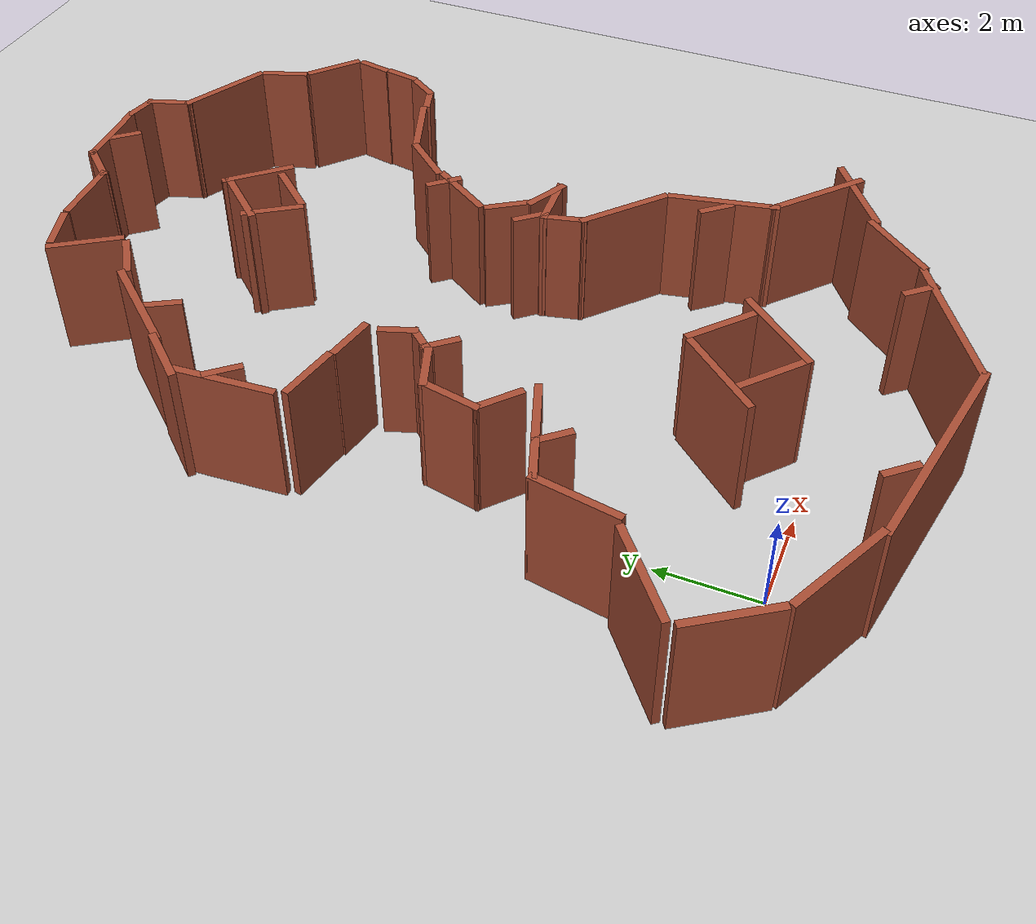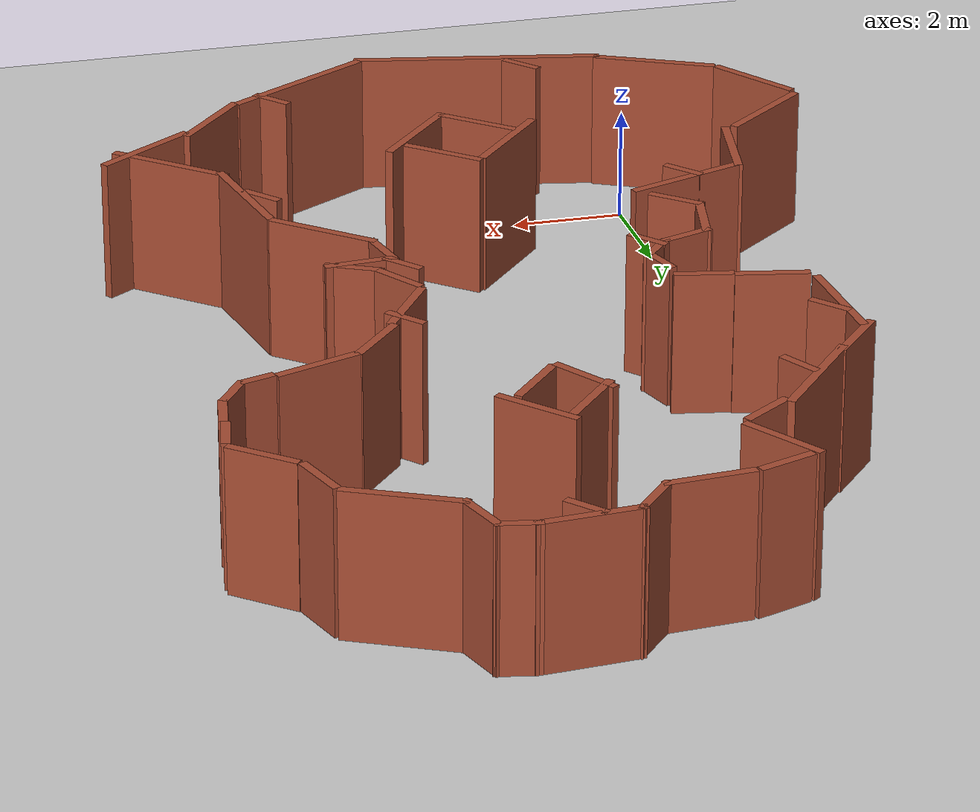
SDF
<sdf version="1.6">
 <world name="default">
  <light name="sun" type="directional">
   <pose>0 0 10 0 -0 0</pose>
   <diffuse>0.8 0.8 0.8 1</diffuse>
   <specular>0.2 0.2 0.2 1</specular>
   <attenuation>
    <range>1000</range>
    <constant>0.9</constant>
    <linear>0.01</linear>
    <quadratic>0.001</quadratic>
   </attenuation>
   <direction>-0.5 0.1 -0.9</direction>
  </light>
  <model name="ground_plane">
   <static>1</static>
   <link name="link">
    <collision name="collision">
     <geometry><plane><normal>0 0 1</normal><size>100 100</size></plane></geometry>
     <surface><friction><ode><mu>100</mu><mu2>50</mu2></ode></friction></surface>
    </collision>
    <visual name="visual">
     <cast_shadows>0</cast_shadows>
     <geometry><plane><normal>0 0 1</normal><size>100 100</size></plane></geometry>
     <material>
      <script><uri>file://media/materials/scripts/gazebo.material</uri><name>Gazebo/Gray</name></script>
     </material>
    </visual>
   </link>
  </model>
  <gravity>0 0 -9.8</gravity>
  <magnetic_field>6e-06 2.3e-05 -4.2e-05</magnetic_field>
  <atmosphere type="adiabatic"/>
  <physics name="default_physics" default="0" type="ode">
   <max_step_size>0.001</max_step_size>
   <real_time_factor>1</real_time_factor>
   <real_time_update_rate>1000</real_time_update_rate>
  </physics>
  <scene><ambient>0.4 0.4 0.4 1</ambient><background>0.7 0.7 0.7 1</background><shadows>1</shadows></scene>
  <spherical_coordinates>
   <surface_model>EARTH_WGS84</surface_model>
   <latitude_deg>0</latitude_deg>
   <longitude_deg>0</longitude_deg>
   <elevation>0</elevation>
   <heading_deg>0</heading_deg>
  </spherical_coordinates>
  <model name="room5">
   <link name="Wall_0">
    <pose>-0.183506 -7.97438 0 0 0 -1.0472</pose>
    <visual name="Wall_0_Visual">
     <pose>0 0 1.25 0 -0 0</pose>
     <geometry><box><size>1 0.15 2.5</size></box></geometry>
     <material>
      <script><uri>file://media/materials/scripts/gazebo.material</uri><name>Gazebo/Bricks</name></script>
      <ambient>1 1 1 1</ambient>
      <shader type="pixel"/>
     </material>
     <meta><layer>0</layer></meta>
    </visual>
    <collision name="Wall_0_Collision">
     <pose>0 0 1.25 0 -0 0</pose>
     <geometry><box><size>1 0.15 2.5</size></box></geometry>
     <surface>
      <friction>
       <ode><mu>1</mu><mu2>1</mu2><fdir1>0 0 0</fdir1><slip1>0</slip1><slip2>0</slip2></ode>
       <torsional>
        <coefficient>1</coefficient>
        <patch_radius>0</patch_radius>
        <surface_radius>0</surface_radius>
        <use_patch_radius>1</use_patch_radius>
        <ode><slip>0</slip></ode>
       </torsional>
      </friction>
      <bounce><restitution_coefficient>0</restitution_coefficient><threshold>1e+06</threshold></bounce>
      <contact>
       <collide_without_contact>0</collide_without_contact>
       <collide_without_contact_bitmask>1</collide_without_contact_bitmask>
       <collide_bitmask>1</collide_bitmask>
       <ode>
        <soft_cfm>0</soft_cfm>
        <soft_erp>0.2</soft_erp>
        <kp>1e+13</kp>
        <kd>1</kd>
        <max_vel>0.01</max_vel>
        <min_depth>0</min_depth>
       </ode>
       <bullet>
        <split_impulse>1</split_impulse>
        <split_impulse_penetration_threshold>-0.01</split_impulse_penetration_threshold>
        <soft_cfm>0</soft_cfm>
        <soft_erp>0.2</soft_erp>
        <kp>1e+13</kp>
        <kd>1</kd>
       </bullet>
      </contact>
     </surface>
    </collision>
   </link>
   <link name="Wall_1">
    <pose>0.328993 -8.34245 0 0 -0 0</pose>
    <visual name="Wall_1_Visual">
     <pose>0 0 1.25 0 -0 0</pose>
     <geometry><box><size>0.75 0.15 2.5</size></box></geometry>
     <material>
      <script><uri>file://media/materials/scripts/gazebo.material</uri><name>Gazebo/Bricks</name></script>
      <ambient>1 1 1 1</ambient>
      <shader type="pixel"/>
     </material>
     <meta><layer>0</layer></meta>
    </visual>
    <collision name="Wall_1_Collision">
     <pose>0 0 1.25 0 -0 0</pose>
     <geometry><box><size>0.75 0.15 2.5</size></box></geometry>
     <surface>
      <friction>
       <ode><mu>1</mu><mu2>1</mu2><fdir1>0 0 0</fdir1><slip1>0</slip1><slip2>0</slip2></ode>
       <torsional>
        <coefficient>1</coefficient>
        <patch_radius>0</patch_radius>
        <surface_radius>0</surface_radius>
        <use_patch_radius>1</use_patch_radius>
        <ode><slip>0</slip></ode>
       </torsional>
      </friction>
      <bounce><restitution_coefficient>0</restitution_coefficient><threshold>1e+06</threshold></bounce>
      <contact>
       <collide_without_contact>0</collide_without_contact>
       <collide_without_contact_bitmask>1</collide_without_contact_bitmask>
       <collide_bitmask>1</collide_bitmask>
       <ode>
        <soft_cfm>0</soft_cfm>
        <soft_erp>0.2</soft_erp>
        <kp>1e+13</kp>
        <kd>1</kd>
        <max_vel>0.01</max_vel>
        <min_depth>0</min_depth>
       </ode>
       <bullet>
        <split_impulse>1</split_impulse>
        <split_impulse_penetration_threshold>-0.01</split_impulse_penetration_threshold>
        <soft_cfm>0</soft_cfm>
        <soft_erp>0.2</soft_erp>
        <kp>1e+13</kp>
        <kd>1</kd>
       </bullet>
      </contact>
     </surface>
    </collision>
   </link>
   <link name="Wall_11">
    <pose>-1.28949 -7.36692 0 0 -0 2.87979</pose>
    <visual name="Wall_11_Visual">
     <pose>0 0 1.25 0 -0 0</pose>
     <geometry><box><size>2 0.15 2.5</size></box></geometry>
     <material>
      <script><uri>file://media/materials/scripts/gazebo.material</uri><name>Gazebo/Bricks</name></script>
      <ambient>1 1 1 1</ambient>
      <shader type="pixel"/>
     </material>
     <meta><layer>0</layer></meta>
    </visual>
    <collision name="Wall_11_Collision">
     <pose>0 0 1.25 0 -0 0</pose>
     <geometry><box><size>2 0.15 2.5</size></box></geometry>
     <surface>
      <friction>
       <ode><mu>1</mu><mu2>1</mu2><fdir1>0 0 0</fdir1><slip1>0</slip1><slip2>0</slip2></ode>
       <torsional>
        <coefficient>1</coefficient>
        <patch_radius>0</patch_radius>
        <surface_radius>0</surface_radius>
        <use_patch_radius>1</use_patch_radius>
        <ode><slip>0</slip></ode>
       </torsional>
      </friction>
      <bounce><restitution_coefficient>0</restitution_coefficient><threshold>1e+06</threshold></bounce>
      <contact>
       <collide_without_contact>0</collide_without_contact>
       <collide_without_contact_bitmask>1</collide_without_contact_bitmask>
       <collide_bitmask>1</collide_bitmask>
       <ode>
        <soft_cfm>0</soft_cfm>
        <soft_erp>0.2</soft_erp>
        <kp>1e+13</kp>
        <kd>1</kd>
        <max_vel>0.01</max_vel>
        <min_depth>0</min_depth>
       </ode>
       <bullet>
        <split_impulse>1</split_impulse>
        <split_impulse_penetration_threshold>-0.01</split_impulse_penetration_threshold>
        <soft_cfm>0</soft_cfm>
        <soft_erp>0.2</soft_erp>
        <kp>1e+13</kp>
        <kd>1</kd>
       </bullet>
      </contact>
     </surface>
    </collision>
   </link>
   <link name="Wall_12">
    <pose>-2.44915 -2.83372 0 0 -0 0.523599</pose>
    <visual name="Wall_12_Visual">
     <pose>0 0 1.25 0 -0 0</pose>
     <geometry><box><size>1.5 0.15 2.5</size></box></geometry>
     <material>
      <script><uri>file://media/materials/scripts/gazebo.material</uri><name>Gazebo/Bricks</name></script>
      <ambient>1 1 1 1</ambient>
      <shader type="pixel"/>
     </material>
     <meta><layer>0</layer></meta>
    </visual>
    <collision name="Wall_12_Collision">
     <pose>0 0 1.25 0 -0 0</pose>
     <geometry><box><size>1.5 0.15 2.5</size></box></geometry>
     <surface>
      <friction>
       <ode><mu>1</mu><mu2>1</mu2><fdir1>0 0 0</fdir1><slip1>0</slip1><slip2>0</slip2></ode>
       <torsional>
        <coefficient>1</coefficient>
        <patch_radius>0</patch_radius>
        <surface_radius>0</surface_radius>
        <use_patch_radius>1</use_patch_radius>
        <ode><slip>0</slip></ode>
       </torsional>
      </friction>
      <bounce><restitution_coefficient>0</restitution_coefficient><threshold>1e+06</threshold></bounce>
      <contact>
       <collide_without_contact>0</collide_without_contact>
       <collide_without_contact_bitmask>1</collide_without_contact_bitmask>
       <collide_bitmask>1</collide_bitmask>
       <ode>
        <soft_cfm>0</soft_cfm>
        <soft_erp>0.2</soft_erp>
        <kp>1e+13</kp>
        <kd>1</kd>
        <max_vel>0.01</max_vel>
        <min_depth>0</min_depth>
       </ode>
       <bullet>
        <split_impulse>1</split_impulse>
        <split_impulse_penetration_threshold>-0.01</split_impulse_penetration_threshold>
        <soft_cfm>0</soft_cfm>
        <soft_erp>0.2</soft_erp>
        <kp>1e+13</kp>
        <kd>1</kd>
       </bullet>
      </contact>
     </surface>
    </collision>
   </link>
   <link name="Wall_13">
    <pose>-2.51054 -6.65573 0 0 -0 2.0944</pose>
    <visual name="Wall_13_Visual">
     <pose>0 0 1.25 0 -0 0</pose>
     <geometry><box><size>1 0.15 2.5</size></box></geometry>
     <material>
      <script><uri>file://media/materials/scripts/gazebo.material</uri><name>Gazebo/Bricks</name></script>
      <ambient>1 1 1 1</ambient>
      <shader type="pixel"/>
     </material>
     <meta><layer>0</layer></meta>
    </visual>
    <collision name="Wall_13_Collision">
     <pose>0 0 1.25 0 -0 0</pose>
     <geometry><box><size>1 0.15 2.5</size></box></geometry>
     <surface>
      <friction>
       <ode><mu>1</mu><mu2>1</mu2><fdir1>0 0 0</fdir1><slip1>0</slip1><slip2>0</slip2></ode>
       <torsional>
        <coefficient>1</coefficient>
        <patch_radius>0</patch_radius>
        <surface_radius>0</surface_radius>
        <use_patch_radius>1</use_patch_radius>
        <ode><slip>0</slip></ode>
       </torsional>
      </friction>
      <bounce><restitution_coefficient>0</restitution_coefficient><threshold>1e+06</threshold></bounce>
      <contact>
       <collide_without_contact>0</collide_without_contact>
       <collide_without_contact_bitmask>1</collide_without_contact_bitmask>
       <collide_bitmask>1</collide_bitmask>
       <ode>
        <soft_cfm>0</soft_cfm>
        <soft_erp>0.2</soft_erp>
        <kp>1e+13</kp>
        <kd>1</kd>
        <max_vel>0.01</max_vel>
        <min_depth>0</min_depth>
       </ode>
       <bullet>
        <split_impulse>1</split_impulse>
        <split_impulse_penetration_threshold>-0.01</split_impulse_penetration_threshold>
        <soft_cfm>0</soft_cfm>
        <soft_erp>0.2</soft_erp>
        <kp>1e+13</kp>
        <kd>1</kd>
       </bullet>
      </contact>
     </surface>
    </collision>
   </link>
   <link name="Wall_16">
    <pose>-3.8903 -5.15429 0 0 -0 1.5708</pose>
    <visual name="Wall_16_Visual">
     <pose>0 0 1.25 0 -0 0</pose>
     <geometry><box><size>0.75 0.15 2.5</size></box></geometry>
     <material>
      <script><uri>file://media/materials/scripts/gazebo.material</uri><name>Gazebo/Bricks</name></script>
      <ambient>1 1 1 1</ambient>
      <shader type="pixel"/>
     </material>
     <meta><layer>0</layer></meta>
    </visual>
    <collision name="Wall_16_Collision">
     <pose>0 0 1.25 0 -0 0</pose>
     <geometry><box><size>0.75 0.15 2.5</size></box></geometry>
     <surface>
      <friction>
       <ode><mu>1</mu><mu2>1</mu2><fdir1>0 0 0</fdir1><slip1>0</slip1><slip2>0</slip2></ode>
       <torsional>
        <coefficient>1</coefficient>
        <patch_radius>0</patch_radius>
        <surface_radius>0</surface_radius>
        <use_patch_radius>1</use_patch_radius>
        <ode><slip>0</slip></ode>
       </torsional>
      </friction>
      <bounce><restitution_coefficient>0</restitution_coefficient><threshold>1e+06</threshold></bounce>
      <contact>
       <collide_without_contact>0</collide_without_contact>
       <collide_without_contact_bitmask>1</collide_without_contact_bitmask>
       <collide_bitmask>1</collide_bitmask>
       <ode>
        <soft_cfm>0</soft_cfm>
        <soft_erp>0.2</soft_erp>
        <kp>1e+13</kp>
        <kd>1</kd>
        <max_vel>0.01</max_vel>
        <min_depth>0</min_depth>
       </ode>
       <bullet>
        <split_impulse>1</split_impulse>
        <split_impulse_penetration_threshold>-0.01</split_impulse_penetration_threshold>
        <soft_cfm>0</soft_cfm>
        <soft_erp>0.2</soft_erp>
        <kp>1e+13</kp>
        <kd>1</kd>
       </bullet>
      </contact>
     </surface>
    </collision>
   </link>
   <link name="Wall_17">
    <pose>-3.33996 -5.9042 0 0 -0 2.63004</pose>
    <visual name="Wall_17_Visual">
     <pose>0 0 1.25 0 -0 0</pose>
     <geometry><box><size>1.25 0.15 2.5</size></box></geometry>
     <material>
      <script><uri>file://media/materials/scripts/gazebo.material</uri><name>Gazebo/Bricks</name></script>
      <ambient>1 1 1 1</ambient>
      <shader type="pixel"/>
     </material>
     <meta><layer>0</layer></meta>
    </visual>
    <collision name="Wall_17_Collision">
     <pose>0 0 1.25 0 -0 0</pose>
     <geometry><box><size>1.25 0.15 2.5</size></box></geometry>
     <surface>
      <friction>
       <ode><mu>1</mu><mu2>1</mu2><fdir1>0 0 0</fdir1><slip1>0</slip1><slip2>0</slip2></ode>
       <torsional>
        <coefficient>1</coefficient>
        <patch_radius>0</patch_radius>
        <surface_radius>0</surface_radius>
        <use_patch_radius>1</use_patch_radius>
        <ode><slip>0</slip></ode>
       </torsional>
      </friction>
      <bounce><restitution_coefficient>0</restitution_coefficient><threshold>1e+06</threshold></bounce>
      <contact>
       <collide_without_contact>0</collide_without_contact>
       <collide_without_contact_bitmask>1</collide_without_contact_bitmask>
       <collide_bitmask>1</collide_bitmask>
       <ode>
        <soft_cfm>0</soft_cfm>
        <soft_erp>0.2</soft_erp>
        <kp>1e+13</kp>
        <kd>1</kd>
        <max_vel>0.01</max_vel>
        <min_depth>0</min_depth>
       </ode>
       <bullet>
        <split_impulse>1</split_impulse>
        <split_impulse_penetration_threshold>-0.01</split_impulse_penetration_threshold>
        <soft_cfm>0</soft_cfm>
        <soft_erp>0.2</soft_erp>
        <kp>1e+13</kp>
        <kd>1</kd>
       </bullet>
      </contact>
     </surface>
    </collision>
   </link>
   <link name="Wall_18">
    <pose>-3.92963 -4.40416 0 0 -0 1.58659</pose>
    <visual name="Wall_18_Visual">
     <pose>0 0 1.25 0 -0 0</pose>
     <geometry><box><size>0.75 0.15 2.5</size></box></geometry>
     <material>
      <script><uri>file://media/materials/scripts/gazebo.material</uri><name>Gazebo/Bricks</name></script>
      <ambient>1 1 1 1</ambient>
      <shader type="pixel"/>
     </material>
     <meta><layer>0</layer></meta>
    </visual>
    <collision name="Wall_18_Collision">
     <pose>0 0 1.25 0 -0 0</pose>
     <geometry><box><size>0.75 0.15 2.5</size></box></geometry>
     <surface>
      <friction>
       <ode><mu>1</mu><mu2>1</mu2><fdir1>0 0 0</fdir1><slip1>0</slip1><slip2>0</slip2></ode>
       <torsional>
        <coefficient>1</coefficient>
        <patch_radius>0</patch_radius>
        <surface_radius>0</surface_radius>
        <use_patch_radius>1</use_patch_radius>
        <ode><slip>0</slip></ode>
       </torsional>
      </friction>
      <bounce><restitution_coefficient>0</restitution_coefficient><threshold>1e+06</threshold></bounce>
      <contact>
       <collide_without_contact>0</collide_without_contact>
       <collide_without_contact_bitmask>1</collide_without_contact_bitmask>
       <collide_bitmask>1</collide_bitmask>
       <ode>
        <soft_cfm>0</soft_cfm>
        <soft_erp>0.2</soft_erp>
        <kp>1e+13</kp>
        <kd>1</kd>
        <max_vel>0.01</max_vel>
        <min_depth>0</min_depth>
       </ode>
       <bullet>
        <split_impulse>1</split_impulse>
        <split_impulse_penetration_threshold>-0.01</split_impulse_penetration_threshold>
        <soft_cfm>0</soft_cfm>
        <soft_erp>0.2</soft_erp>
        <kp>1e+13</kp>
        <kd>1</kd>
       </bullet>
      </contact>
     </surface>
    </collision>
   </link>
   <link name="Wall_2">
    <pose>1.40173 -8.13539 0 0 -0 0.261799</pose>
    <visual name="Wall_2_Visual">
     <pose>0 0 1.25 0 -0 0</pose>
     <geometry><box><size>1.75 0.15 2.5</size></box></geometry>
     <material>
      <script><uri>file://media/materials/scripts/gazebo.material</uri><name>Gazebo/Bricks</name></script>
      <ambient>1 1 1 1</ambient>
      <shader type="pixel"/>
     </material>
     <meta><layer>0</layer></meta>
    </visual>
    <collision name="Wall_2_Collision">
     <pose>0 0 1.25 0 -0 0</pose>
     <geometry><box><size>1.75 0.15 2.5</size></box></geometry>
     <surface>
      <friction>
       <ode><mu>1</mu><mu2>1</mu2><fdir1>0 0 0</fdir1><slip1>0</slip1><slip2>0</slip2></ode>
       <torsional>
        <coefficient>1</coefficient>
        <patch_radius>0</patch_radius>
        <surface_radius>0</surface_radius>
        <use_patch_radius>1</use_patch_radius>
        <ode><slip>0</slip></ode>
       </torsional>
      </friction>
      <bounce><restitution_coefficient>0</restitution_coefficient><threshold>1e+06</threshold></bounce>
      <contact>
       <collide_without_contact>0</collide_without_contact>
       <collide_without_contact_bitmask>1</collide_without_contact_bitmask>
       <collide_bitmask>1</collide_bitmask>
       <ode>
        <soft_cfm>0</soft_cfm>
        <soft_erp>0.2</soft_erp>
        <kp>1e+13</kp>
        <kd>1</kd>
        <max_vel>0.01</max_vel>
        <min_depth>0</min_depth>
       </ode>
       <bullet>
        <split_impulse>1</split_impulse>
        <split_impulse_penetration_threshold>-0.01</split_impulse_penetration_threshold>
        <soft_cfm>0</soft_cfm>
        <soft_erp>0.2</soft_erp>
        <kp>1e+13</kp>
        <kd>1</kd>
       </bullet>
      </contact>
     </surface>
    </collision>
   </link>
   <link name="Wall_20">
    <pose>-1.49461 -1.95686 0 0 -0 1.0472</pose>
    <visual name="Wall_20_Visual">
     <pose>0 0 1.25 0 -0 0</pose>
     <geometry><box><size>1.25 0.15 2.5</size></box></geometry>
     <material>
      <script><uri>file://media/materials/scripts/gazebo.material</uri><name>Gazebo/Bricks</name></script>
      <ambient>1 1 1 1</ambient>
      <shader type="pixel"/>
     </material>
     <meta><layer>0</layer></meta>
    </visual>
    <collision name="Wall_20_Collision">
     <pose>0 0 1.25 0 -0 0</pose>
     <geometry><box><size>1.25 0.15 2.5</size></box></geometry>
     <surface>
      <friction>
       <ode><mu>1</mu><mu2>1</mu2><fdir1>0 0 0</fdir1><slip1>0</slip1><slip2>0</slip2></ode>
       <torsional>
        <coefficient>1</coefficient>
        <patch_radius>0</patch_radius>
        <surface_radius>0</surface_radius>
        <use_patch_radius>1</use_patch_radius>
        <ode><slip>0</slip></ode>
       </torsional>
      </friction>
      <bounce><restitution_coefficient>0</restitution_coefficient><threshold>1e+06</threshold></bounce>
      <contact>
       <collide_without_contact>0</collide_without_contact>
       <collide_without_contact_bitmask>1</collide_without_contact_bitmask>
       <collide_bitmask>1</collide_bitmask>
       <ode>
        <soft_cfm>0</soft_cfm>
        <soft_erp>0.2</soft_erp>
        <kp>1e+13</kp>
        <kd>1</kd>
        <max_vel>0.01</max_vel>
        <min_depth>0</min_depth>
       </ode>
       <bullet>
        <split_impulse>1</split_impulse>
        <split_impulse_penetration_threshold>-0.01</split_impulse_penetration_threshold>
        <soft_cfm>0</soft_cfm>
        <soft_erp>0.2</soft_erp>
        <kp>1e+13</kp>
        <kd>1</kd>
       </bullet>
      </contact>
     </surface>
    </collision>
   </link>
   <link name="Wall_21">
    <pose>-3.77154 -3.72157 0 0 -0 1.16555</pose>
    <visual name="Wall_21_Visual">
     <pose>0 0 1.25 0 -0 0</pose>
     <geometry><box><size>0.75 0.15 2.5</size></box></geometry>
     <material>
      <script><uri>file://media/materials/scripts/gazebo.material</uri><name>Gazebo/Bricks</name></script>
      <ambient>1 1 1 1</ambient>
      <shader type="pixel"/>
     </material>
     <meta><layer>0</layer></meta>
    </visual>
    <collision name="Wall_21_Collision">
     <pose>0 0 1.25 0 -0 0</pose>
     <geometry><box><size>0.75 0.15 2.5</size></box></geometry>
     <surface>
      <friction>
       <ode><mu>1</mu><mu2>1</mu2><fdir1>0 0 0</fdir1><slip1>0</slip1><slip2>0</slip2></ode>
       <torsional>
        <coefficient>1</coefficient>
        <patch_radius>0</patch_radius>
        <surface_radius>0</surface_radius>
        <use_patch_radius>1</use_patch_radius>
        <ode><slip>0</slip></ode>
       </torsional>
      </friction>
      <bounce><restitution_coefficient>0</restitution_coefficient><threshold>1e+06</threshold></bounce>
      <contact>
       <collide_without_contact>0</collide_without_contact>
       <collide_without_contact_bitmask>1</collide_without_contact_bitmask>
       <collide_bitmask>1</collide_bitmask>
       <ode>
        <soft_cfm>0</soft_cfm>
        <soft_erp>0.2</soft_erp>
        <kp>1e+13</kp>
        <kd>1</kd>
        <max_vel>0.01</max_vel>
        <min_depth>0</min_depth>
       </ode>
       <bullet>
        <split_impulse>1</split_impulse>
        <split_impulse_penetration_threshold>-0.01</split_impulse_penetration_threshold>
        <soft_cfm>0</soft_cfm>
        <soft_erp>0.2</soft_erp>
        <kp>1e+13</kp>
        <kd>1</kd>
       </bullet>
      </contact>
     </surface>
    </collision>
   </link>
   <link name="Wall_23">
    <pose>-0.971243 -0.724123 0 0 -0 1.18423</pose>
    <visual name="Wall_23_Visual">
     <pose>0 0 1.25 0 -0 0</pose>
     <geometry><box><size>1.5 0.15 2.5</size></box></geometry>
     <material>
      <script><uri>file://media/materials/scripts/gazebo.material</uri><name>Gazebo/Bricks</name></script>
      <ambient>1 1 1 1</ambient>
      <shader type="pixel"/>
     </material>
     <meta><layer>0</layer></meta>
    </visual>
    <collision name="Wall_23_Collision">
     <pose>0 0 1.25 0 -0 0</pose>
     <geometry><box><size>1.5 0.15 2.5</size></box></geometry>
     <surface>
      <friction>
       <ode><mu>1</mu><mu2>1</mu2><fdir1>0 0 0</fdir1><slip1>0</slip1><slip2>0</slip2></ode>
       <torsional>
        <coefficient>1</coefficient>
        <patch_radius>0</patch_radius>
        <surface_radius>0</surface_radius>
        <use_patch_radius>1</use_patch_radius>
        <ode><slip>0</slip></ode>
       </torsional>
      </friction>
      <bounce><restitution_coefficient>0</restitution_coefficient><threshold>1e+06</threshold></bounce>
      <contact>
       <collide_without_contact>0</collide_without_contact>
       <collide_without_contact_bitmask>1</collide_without_contact_bitmask>
       <collide_bitmask>1</collide_bitmask>
       <ode>
        <soft_cfm>0</soft_cfm>
        <soft_erp>0.2</soft_erp>
        <kp>1e+13</kp>
        <kd>1</kd>
        <max_vel>0.01</max_vel>
        <min_depth>0</min_depth>
       </ode>
       <bullet>
        <split_impulse>1</split_impulse>
        <split_impulse_penetration_threshold>-0.01</split_impulse_penetration_threshold>
        <soft_cfm>0</soft_cfm>
        <soft_erp>0.2</soft_erp>
        <kp>1e+13</kp>
        <kd>1</kd>
       </bullet>
      </contact>
     </surface>
    </collision>
   </link>
   <link name="Wall_24">
    <pose>-1.05323 0.370394 0 0 -0 2.35619</pose>
    <visual name="Wall_24_Visual">
     <pose>0 0 1.25 0 -0 0</pose>
     <geometry><box><size>1 0.15 2.5</size></box></geometry>
     <material>
      <script><uri>file://media/materials/scripts/gazebo.material</uri><name>Gazebo/Bricks</name></script>
      <ambient>1 1 1 1</ambient>
      <shader type="pixel"/>
     </material>
     <meta><layer>0</layer></meta>
    </visual>
    <collision name="Wall_24_Collision">
     <pose>0 0 1.25 0 -0 0</pose>
     <geometry><box><size>1 0.15 2.5</size></box></geometry>
     <surface>
      <friction>
       <ode><mu>1</mu><mu2>1</mu2><fdir1>0 0 0</fdir1><slip1>0</slip1><slip2>0</slip2></ode>
       <torsional>
        <coefficient>1</coefficient>
        <patch_radius>0</patch_radius>
        <surface_radius>0</surface_radius>
        <use_patch_radius>1</use_patch_radius>
        <ode><slip>0</slip></ode>
       </torsional>
      </friction>
      <bounce><restitution_coefficient>0</restitution_coefficient><threshold>1e+06</threshold></bounce>
      <contact>
       <collide_without_contact>0</collide_without_contact>
       <collide_without_contact_bitmask>1</collide_without_contact_bitmask>
       <collide_bitmask>1</collide_bitmask>
       <ode>
        <soft_cfm>0</soft_cfm>
        <soft_erp>0.2</soft_erp>
        <kp>1e+13</kp>
        <kd>1</kd>
        <max_vel>0.01</max_vel>
        <min_depth>0</min_depth>
       </ode>
       <bullet>
        <split_impulse>1</split_impulse>
        <split_impulse_penetration_threshold>-0.01</split_impulse_penetration_threshold>
        <soft_cfm>0</soft_cfm>
        <soft_erp>0.2</soft_erp>
        <kp>1e+13</kp>
        <kd>1</kd>
       </bullet>
      </contact>
     </surface>
    </collision>
   </link>
   <link name="Wall_25">
    <pose>-1.76805 0.819479 0 0 -0 2.87979</pose>
    <visual name="Wall_25_Visual">
     <pose>0 0 1.25 0 -0 0</pose>
     <geometry><box><size>1 0.15 2.5</size></box></geometry>
     <material>
      <script><uri>file://media/materials/scripts/gazebo.material</uri><name>Gazebo/Bricks</name></script>
      <ambient>1 1 1 1</ambient>
      <shader type="pixel"/>
     </material>
     <meta><layer>0</layer></meta>
    </visual>
    <collision name="Wall_25_Collision">
     <pose>0 0 1.25 0 -0 0</pose>
     <geometry><box><size>1 0.15 2.5</size></box></geometry>
     <surface>
      <friction>
       <ode><mu>1</mu><mu2>1</mu2><fdir1>0 0 0</fdir1><slip1>0</slip1><slip2>0</slip2></ode>
       <torsional>
        <coefficient>1</coefficient>
        <patch_radius>0</patch_radius>
        <surface_radius>0</surface_radius>
        <use_patch_radius>1</use_patch_radius>
        <ode><slip>0</slip></ode>
       </torsional>
      </friction>
      <bounce><restitution_coefficient>0</restitution_coefficient><threshold>1e+06</threshold></bounce>
      <contact>
       <collide_without_contact>0</collide_without_contact>
       <collide_without_contact_bitmask>1</collide_without_contact_bitmask>
       <collide_bitmask>1</collide_bitmask>
       <ode>
        <soft_cfm>0</soft_cfm>
        <soft_erp>0.2</soft_erp>
        <kp>1e+13</kp>
        <kd>1</kd>
        <max_vel>0.01</max_vel>
        <min_depth>0</min_depth>
       </ode>
       <bullet>
        <split_impulse>1</split_impulse>
        <split_impulse_penetration_threshold>-0.01</split_impulse_penetration_threshold>
        <soft_cfm>0</soft_cfm>
        <soft_erp>0.2</soft_erp>
        <kp>1e+13</kp>
        <kd>1</kd>
       </bullet>
      </contact>
     </surface>
    </collision>
   </link>
   <link name="Wall_26">
    <pose>-1.64353 1.03326 0 0 -0 0.261799</pose>
    <visual name="Wall_26_Visual">
     <pose>0 0 1.25 0 -0 0</pose>
     <geometry><box><size>1.25 0.15 2.5</size></box></geometry>
     <material>
      <script><uri>file://media/materials/scripts/gazebo.material</uri><name>Gazebo/Bricks</name></script>
      <ambient>1 1 1 1</ambient>
      <shader type="pixel"/>
     </material>
     <meta><layer>0</layer></meta>
    </visual>
    <collision name="Wall_26_Collision">
     <pose>0 0 1.25 0 -0 0</pose>
     <geometry><box><size>1.25 0.15 2.5</size></box></geometry>
     <surface>
      <friction>
       <ode><mu>1</mu><mu2>1</mu2><fdir1>0 0 0</fdir1><slip1>0</slip1><slip2>0</slip2></ode>
       <torsional>
        <coefficient>1</coefficient>
        <patch_radius>0</patch_radius>
        <surface_radius>0</surface_radius>
        <use_patch_radius>1</use_patch_radius>
        <ode><slip>0</slip></ode>
       </torsional>
      </friction>
      <bounce><restitution_coefficient>0</restitution_coefficient><threshold>1e+06</threshold></bounce>
      <contact>
       <collide_without_contact>0</collide_without_contact>
       <collide_without_contact_bitmask>1</collide_without_contact_bitmask>
       <collide_bitmask>1</collide_bitmask>
       <ode>
        <soft_cfm>0</soft_cfm>
        <soft_erp>0.2</soft_erp>
        <kp>1e+13</kp>
        <kd>1</kd>
        <max_vel>0.01</max_vel>
        <min_depth>0</min_depth>
       </ode>
       <bullet>
        <split_impulse>1</split_impulse>
        <split_impulse_penetration_threshold>-0.01</split_impulse_penetration_threshold>
        <soft_cfm>0</soft_cfm>
        <soft_erp>0.2</soft_erp>
        <kp>1e+13</kp>
        <kd>1</kd>
       </bullet>
      </contact>
     </surface>
    </collision>
   </link>
   <link name="Wall_3">
    <pose>2.38698 -7.56027 0 0 -0 1.0472</pose>
    <visual name="Wall_3_Visual">
     <pose>0 0 1.25 0 -0 0</pose>
     <geometry><box><size>1 0.15 2.5</size></box></geometry>
     <material>
      <script><uri>file://media/materials/scripts/gazebo.material</uri><name>Gazebo/Bricks</name></script>
      <ambient>1 1 1 1</ambient>
      <shader type="pixel"/>
     </material>
     <meta><layer>0</layer></meta>
    </visual>
    <collision name="Wall_3_Collision">
     <pose>0 0 1.25 0 -0 0</pose>
     <geometry><box><size>1 0.15 2.5</size></box></geometry>
     <surface>
      <friction>
       <ode><mu>1</mu><mu2>1</mu2><fdir1>0 0 0</fdir1><slip1>0</slip1><slip2>0</slip2></ode>
       <torsional>
        <coefficient>1</coefficient>
        <patch_radius>0</patch_radius>
        <surface_radius>0</surface_radius>
        <use_patch_radius>1</use_patch_radius>
        <ode><slip>0</slip></ode>
       </torsional>
      </friction>
      <bounce><restitution_coefficient>0</restitution_coefficient><threshold>1e+06</threshold></bounce>
      <contact>
       <collide_without_contact>0</collide_without_contact>
       <collide_without_contact_bitmask>1</collide_without_contact_bitmask>
       <collide_bitmask>1</collide_bitmask>
       <ode>
        <soft_cfm>0</soft_cfm>
        <soft_erp>0.2</soft_erp>
        <kp>1e+13</kp>
        <kd>1</kd>
        <max_vel>0.01</max_vel>
        <min_depth>0</min_depth>
       </ode>
       <bullet>
        <split_impulse>1</split_impulse>
        <split_impulse_penetration_threshold>-0.01</split_impulse_penetration_threshold>
        <soft_cfm>0</soft_cfm>
        <soft_erp>0.2</soft_erp>
        <kp>1e+13</kp>
        <kd>1</kd>
       </bullet>
      </contact>
     </surface>
    </collision>
   </link>
   <link name="Wall_32">
    <pose>5.28652 -3.58139 0 0 -0 1.07102</pose>
    <visual name="Wall_32_Visual">
     <pose>0 0 1.25 0 -0 0</pose>
     <geometry><box><size>2.25 0.15 2.5</size></box></geometry>
     <material>
      <script><uri>file://media/materials/scripts/gazebo.material</uri><name>Gazebo/Bricks</name></script>
      <ambient>1 1 1 1</ambient>
      <shader type="pixel"/>
     </material>
     <meta><layer>0</layer></meta>
    </visual>
    <collision name="Wall_32_Collision">
     <pose>0 0 1.25 0 -0 0</pose>
     <geometry><box><size>2.25 0.15 2.5</size></box></geometry>
     <surface>
      <friction>
       <ode><mu>1</mu><mu2>1</mu2><fdir1>0 0 0</fdir1><slip1>0</slip1><slip2>0</slip2></ode>
       <torsional>
        <coefficient>1</coefficient>
        <patch_radius>0</patch_radius>
        <surface_radius>0</surface_radius>
        <use_patch_radius>1</use_patch_radius>
        <ode><slip>0</slip></ode>
       </torsional>
      </friction>
      <bounce><restitution_coefficient>0</restitution_coefficient><threshold>1e+06</threshold></bounce>
      <contact>
       <collide_without_contact>0</collide_without_contact>
       <collide_without_contact_bitmask>1</collide_without_contact_bitmask>
       <collide_bitmask>1</collide_bitmask>
       <ode>
        <soft_cfm>0</soft_cfm>
        <soft_erp>0.2</soft_erp>
        <kp>1e+13</kp>
        <kd>1</kd>
        <max_vel>0.01</max_vel>
        <min_depth>0</min_depth>
       </ode>
       <bullet>
        <split_impulse>1</split_impulse>
        <split_impulse_penetration_threshold>-0.01</split_impulse_penetration_threshold>
        <soft_cfm>0</soft_cfm>
        <soft_erp>0.2</soft_erp>
        <kp>1e+13</kp>
        <kd>1</kd>
       </bullet>
      </contact>
     </surface>
    </collision>
   </link>
   <link name="Wall_33">
    <pose>5.99667 -0.885929 0 0 -0 1.8326</pose>
    <visual name="Wall_33_Visual">
     <pose>0 0 1.25 0 -0 0</pose>
     <geometry><box><size>2 0.15 2.5</size></box></geometry>
     <material>
      <script><uri>file://media/materials/scripts/gazebo.material</uri><name>Gazebo/Bricks</name></script>
      <ambient>1 1 1 1</ambient>
      <shader type="pixel"/>
     </material>
     <meta><layer>0</layer></meta>
    </visual>
    <collision name="Wall_33_Collision">
     <pose>0 0 1.25 0 -0 0</pose>
     <geometry><box><size>2 0.15 2.5</size></box></geometry>
     <surface>
      <friction>
       <ode><mu>1</mu><mu2>1</mu2><fdir1>0 0 0</fdir1><slip1>0</slip1><slip2>0</slip2></ode>
       <torsional>
        <coefficient>1</coefficient>
        <patch_radius>0</patch_radius>
        <surface_radius>0</surface_radius>
        <use_patch_radius>1</use_patch_radius>
        <ode><slip>0</slip></ode>
       </torsional>
      </friction>
      <bounce><restitution_coefficient>0</restitution_coefficient><threshold>1e+06</threshold></bounce>
      <contact>
       <collide_without_contact>0</collide_without_contact>
       <collide_without_contact_bitmask>1</collide_without_contact_bitmask>
       <collide_bitmask>1</collide_bitmask>
       <ode>
        <soft_cfm>0</soft_cfm>
        <soft_erp>0.2</soft_erp>
        <kp>1e+13</kp>
        <kd>1</kd>
        <max_vel>0.01</max_vel>
        <min_depth>0</min_depth>
       </ode>
       <bullet>
        <split_impulse>1</split_impulse>
        <split_impulse_penetration_threshold>-0.01</split_impulse_penetration_threshold>
        <soft_cfm>0</soft_cfm>
        <soft_erp>0.2</soft_erp>
        <kp>1e+13</kp>
        <kd>1</kd>
       </bullet>
      </contact>
     </surface>
    </collision>
   </link>
   <link name="Wall_34">
    <pose>5.03984 0.226363 0 0 -0 0</pose>
    <visual name="Wall_34_Visual">
     <pose>0 0 1.25 0 -0 0</pose>
     <geometry><box><size>1.25 0.15 2.5</size></box></geometry>
     <material>
      <script><uri>file://media/materials/scripts/gazebo.material</uri><name>Gazebo/Bricks</name></script>
      <ambient>1 1 1 1</ambient>
      <shader type="pixel"/>
     </material>
     <meta><layer>0</layer></meta>
    </visual>
    <collision name="Wall_34_Collision">
     <pose>0 0 1.25 0 -0 0</pose>
     <geometry><box><size>1.25 0.15 2.5</size></box></geometry>
     <surface>
      <friction>
       <ode><mu>1</mu><mu2>1</mu2><fdir1>0 0 0</fdir1><slip1>0</slip1><slip2>0</slip2></ode>
       <torsional>
        <coefficient>1</coefficient>
        <patch_radius>0</patch_radius>
        <surface_radius>0</surface_radius>
        <use_patch_radius>1</use_patch_radius>
        <ode><slip>0</slip></ode>
       </torsional>
      </friction>
      <bounce><restitution_coefficient>0</restitution_coefficient><threshold>1e+06</threshold></bounce>
      <contact>
       <collide_without_contact>0</collide_without_contact>
       <collide_without_contact_bitmask>1</collide_without_contact_bitmask>
       <collide_bitmask>1</collide_bitmask>
       <ode>
        <soft_cfm>0</soft_cfm>
        <soft_erp>0.2</soft_erp>
        <kp>1e+13</kp>
        <kd>1</kd>
        <max_vel>0.01</max_vel>
        <min_depth>0</min_depth>
       </ode>
       <bullet>
        <split_impulse>1</split_impulse>
        <split_impulse_penetration_threshold>-0.01</split_impulse_penetration_threshold>
        <soft_cfm>0</soft_cfm>
        <soft_erp>0.2</soft_erp>
        <kp>1e+13</kp>
        <kd>1</kd>
       </bullet>
      </contact>
     </surface>
    </collision>
   </link>
   <link name="Wall_35">
    <pose>6.08077 -2.2305 0 0 -0 1.0472</pose>
    <visual name="Wall_35_Visual">
     <pose>0 0 1.25 0 -0 0</pose>
     <geometry><box><size>1.25 0.15 2.5</size></box></geometry>
     <material>
      <script><uri>file://media/materials/scripts/gazebo.material</uri><name>Gazebo/Bricks</name></script>
      <ambient>1 1 1 1</ambient>
      <shader type="pixel"/>
     </material>
     <meta><layer>0</layer></meta>
    </visual>
    <collision name="Wall_35_Collision">
     <pose>0 0 1.25 0 -0 0</pose>
     <geometry><box><size>1.25 0.15 2.5</size></box></geometry>
     <surface>
      <friction>
       <ode><mu>1</mu><mu2>1</mu2><fdir1>0 0 0</fdir1><slip1>0</slip1><slip2>0</slip2></ode>
       <torsional>
        <coefficient>1</coefficient>
        <patch_radius>0</patch_radius>
        <surface_radius>0</surface_radius>
        <use_patch_radius>1</use_patch_radius>
        <ode><slip>0</slip></ode>
       </torsional>
      </friction>
      <bounce><restitution_coefficient>0</restitution_coefficient><threshold>1e+06</threshold></bounce>
      <contact>
       <collide_without_contact>0</collide_without_contact>
       <collide_without_contact_bitmask>1</collide_without_contact_bitmask>
       <collide_bitmask>1</collide_bitmask>
       <ode>
        <soft_cfm>0</soft_cfm>
        <soft_erp>0.2</soft_erp>
        <kp>1e+13</kp>
        <kd>1</kd>
        <max_vel>0.01</max_vel>
        <min_depth>0</min_depth>
       </ode>
       <bullet>
        <split_impulse>1</split_impulse>
        <split_impulse_penetration_threshold>-0.01</split_impulse_penetration_threshold>
        <soft_cfm>0</soft_cfm>
        <soft_erp>0.2</soft_erp>
        <kp>1e+13</kp>
        <kd>1</kd>
       </bullet>
      </contact>
     </surface>
    </collision>
   </link>
   <link name="Wall_36">
    <pose>3.91729 0.265768 0 0 -0 3.14159</pose>
    <visual name="Wall_36_Visual">
     <pose>0 0 1.25 0 -0 0</pose>
     <geometry><box><size>1 0.15 2.5</size></box></geometry>
     <material>
      <script><uri>file://media/materials/scripts/gazebo.material</uri><name>Gazebo/Bricks</name></script>
      <ambient>1 1 1 1</ambient>
      <shader type="pixel"/>
     </material>
     <meta><layer>0</layer></meta>
    </visual>
    <collision name="Wall_36_Collision">
     <pose>0 0 1.25 0 -0 0</pose>
     <geometry><box><size>1 0.15 2.5</size></box></geometry>
     <surface>
      <friction>
       <ode><mu>1</mu><mu2>1</mu2><fdir1>0 0 0</fdir1><slip1>0</slip1><slip2>0</slip2></ode>
       <torsional>
        <coefficient>1</coefficient>
        <patch_radius>0</patch_radius>
        <surface_radius>0</surface_radius>
        <use_patch_radius>1</use_patch_radius>
        <ode><slip>0</slip></ode>
       </torsional>
      </friction>
      <bounce><restitution_coefficient>0</restitution_coefficient><threshold>1e+06</threshold></bounce>
      <contact>
       <collide_without_contact>0</collide_without_contact>
       <collide_without_contact_bitmask>1</collide_without_contact_bitmask>
       <collide_bitmask>1</collide_bitmask>
       <ode>
        <soft_cfm>0</soft_cfm>
        <soft_erp>0.2</soft_erp>
        <kp>1e+13</kp>
        <kd>1</kd>
        <max_vel>0.01</max_vel>
        <min_depth>0</min_depth>
       </ode>
       <bullet>
        <split_impulse>1</split_impulse>
        <split_impulse_penetration_threshold>-0.01</split_impulse_penetration_threshold>
        <soft_cfm>0</soft_cfm>
        <soft_erp>0.2</soft_erp>
        <kp>1e+13</kp>
        <kd>1</kd>
       </bullet>
      </contact>
     </surface>
    </collision>
   </link>
   <link name="Wall_37">
    <pose>3.25761 0.842357 0 0 -0 2.0944</pose>
    <visual name="Wall_37_Visual">
     <pose>0 0 1.25 0 -0 0</pose>
     <geometry><box><size>0.75 0.15 2.5</size></box></geometry>
     <material>
      <script><uri>file://media/materials/scripts/gazebo.material</uri><name>Gazebo/Bricks</name></script>
      <ambient>1 1 1 1</ambient>
      <shader type="pixel"/>
     </material>
     <meta><layer>0</layer></meta>
    </visual>
    <collision name="Wall_37_Collision">
     <pose>0 0 1.25 0 -0 0</pose>
     <geometry><box><size>0.75 0.15 2.5</size></box></geometry>
     <surface>
      <friction>
       <ode><mu>1</mu><mu2>1</mu2><fdir1>0 0 0</fdir1><slip1>0</slip1><slip2>0</slip2></ode>
       <torsional>
        <coefficient>1</coefficient>
        <patch_radius>0</patch_radius>
        <surface_radius>0</surface_radius>
        <use_patch_radius>1</use_patch_radius>
        <ode><slip>0</slip></ode>
       </torsional>
      </friction>
      <bounce><restitution_coefficient>0</restitution_coefficient><threshold>1e+06</threshold></bounce>
      <contact>
       <collide_without_contact>0</collide_without_contact>
       <collide_without_contact_bitmask>1</collide_without_contact_bitmask>
       <collide_bitmask>1</collide_bitmask>
       <ode>
        <soft_cfm>0</soft_cfm>
        <soft_erp>0.2</soft_erp>
        <kp>1e+13</kp>
        <kd>1</kd>
        <max_vel>0.01</max_vel>
        <min_depth>0</min_depth>
       </ode>
       <bullet>
        <split_impulse>1</split_impulse>
        <split_impulse_penetration_threshold>-0.01</split_impulse_penetration_threshold>
        <soft_cfm>0</soft_cfm>
        <soft_erp>0.2</soft_erp>
        <kp>1e+13</kp>
        <kd>1</kd>
       </bullet>
      </contact>
     </surface>
    </collision>
   </link>
   <link name="Wall_37_clone">
    <pose>5.05026 -3.21576 0 0 0 -0.85261</pose>
    <visual name="Wall_37_Visual">
     <pose>0 0 1.25 0 -0 0</pose>
     <geometry><box><size>0.75 0.15 2.5</size></box></geometry>
     <material>
      <script><uri>file://media/materials/scripts/gazebo.material</uri><name>Gazebo/Bricks</name></script>
      <ambient>1 1 1 1</ambient>
      <shader type="pixel"/>
     </material>
     <meta><layer>0</layer></meta>
    </visual>
    <collision name="Wall_37_Collision">
     <pose>0 0 1.25 0 -0 0</pose>
     <geometry><box><size>0.75 0.15 2.5</size></box></geometry>
     <surface>
      <friction>
       <ode><mu>1</mu><mu2>1</mu2><fdir1>0 0 0</fdir1><slip1>0</slip1><slip2>0</slip2></ode>
       <torsional>
        <coefficient>1</coefficient>
        <patch_radius>0</patch_radius>
        <surface_radius>0</surface_radius>
        <use_patch_radius>1</use_patch_radius>
        <ode><slip>0</slip></ode>
       </torsional>
      </friction>
      <bounce><restitution_coefficient>0</restitution_coefficient><threshold>1e+06</threshold></bounce>
      <contact>
       <collide_without_contact>0</collide_without_contact>
       <collide_without_contact_bitmask>1</collide_without_contact_bitmask>
       <collide_bitmask>1</collide_bitmask>
       <ode>
        <soft_cfm>0</soft_cfm>
        <soft_erp>0.2</soft_erp>
        <kp>1e+13</kp>
        <kd>1</kd>
        <max_vel>0.01</max_vel>
        <min_depth>0</min_depth>
       </ode>
       <bullet>
        <split_impulse>1</split_impulse>
        <split_impulse_penetration_threshold>-0.01</split_impulse_penetration_threshold>
        <soft_cfm>0</soft_cfm>
        <soft_erp>0.2</soft_erp>
        <kp>1e+13</kp>
        <kd>1</kd>
       </bullet>
      </contact>
     </surface>
    </collision>
   </link>
   <link name="Wall_37_clone_clone">
    <pose>-1.0031 -1.17645 0 0 -0 2.48357</pose>
    <visual name="Wall_37_Visual">
     <pose>0 0 1.25 0 -0 0</pose>
     <geometry><box><size>0.75 0.15 2.5</size></box></geometry>
     <material>
      <script><uri>file://media/materials/scripts/gazebo.material</uri><name>Gazebo/Bricks</name></script>
      <ambient>1 1 1 1</ambient>
      <shader type="pixel"/>
     </material>
     <meta><layer>0</layer></meta>
    </visual>
    <collision name="Wall_37_Collision">
     <pose>0 0 1.25 0 -0 0</pose>
     <geometry><box><size>0.75 0.15 2.5</size></box></geometry>
     <surface>
      <friction>
       <ode><mu>1</mu><mu2>1</mu2><fdir1>0 0 0</fdir1><slip1>0</slip1><slip2>0</slip2></ode>
       <torsional>
        <coefficient>1</coefficient>
        <patch_radius>0</patch_radius>
        <surface_radius>0</surface_radius>
        <use_patch_radius>1</use_patch_radius>
        <ode><slip>0</slip></ode>
       </torsional>
      </friction>
      <bounce><restitution_coefficient>0</restitution_coefficient><threshold>1e+06</threshold></bounce>
      <contact>
       <collide_without_contact>0</collide_without_contact>
       <collide_without_contact_bitmask>1</collide_without_contact_bitmask>
       <collide_bitmask>1</collide_bitmask>
       <ode>
        <soft_cfm>0</soft_cfm>
        <soft_erp>0.2</soft_erp>
        <kp>1e+13</kp>
        <kd>1</kd>
        <max_vel>0.01</max_vel>
        <min_depth>0</min_depth>
       </ode>
       <bullet>
        <split_impulse>1</split_impulse>
        <split_impulse_penetration_threshold>-0.01</split_impulse_penetration_threshold>
        <soft_cfm>0</soft_cfm>
        <soft_erp>0.2</soft_erp>
        <kp>1e+13</kp>
        <kd>1</kd>
       </bullet>
      </contact>
     </surface>
    </collision>
   </link>
   <link name="Wall_37_clone_clone_0">
    <pose>1.55945 9.7192 0 0 -0 2.48357</pose>
    <visual name="Wall_37_Visual">
     <pose>0 0 1.25 0 -0 0</pose>
     <geometry><box><size>0.75 0.15 2.5</size></box></geometry>
     <material>
      <script><uri>file://media/materials/scripts/gazebo.material</uri><name>Gazebo/Bricks</name></script>
      <ambient>1 1 1 1</ambient>
      <shader type="pixel"/>
     </material>
     <meta><layer>0</layer></meta>
    </visual>
    <collision name="Wall_37_Collision">
     <pose>0 0 1.25 0 -0 0</pose>
     <geometry><box><size>0.75 0.15 2.5</size></box></geometry>
     <surface>
      <friction>
       <ode><mu>1</mu><mu2>1</mu2><fdir1>0 0 0</fdir1><slip1>0</slip1><slip2>0</slip2></ode>
       <torsional>
        <coefficient>1</coefficient>
        <patch_radius>0</patch_radius>
        <surface_radius>0</surface_radius>
        <use_patch_radius>1</use_patch_radius>
        <ode><slip>0</slip></ode>
       </torsional>
      </friction>
      <bounce><restitution_coefficient>0</restitution_coefficient><threshold>1e+06</threshold></bounce>
      <contact>
       <collide_without_contact>0</collide_without_contact>
       <collide_without_contact_bitmask>1</collide_without_contact_bitmask>
       <collide_bitmask>1</collide_bitmask>
       <ode>
        <soft_cfm>0</soft_cfm>
        <soft_erp>0.2</soft_erp>
        <kp>1e+13</kp>
        <kd>1</kd>
        <max_vel>0.01</max_vel>
        <min_depth>0</min_depth>
       </ode>
       <bullet>
        <split_impulse>1</split_impulse>
        <split_impulse_penetration_threshold>-0.01</split_impulse_penetration_threshold>
        <soft_cfm>0</soft_cfm>
        <soft_erp>0.2</soft_erp>
        <kp>1e+13</kp>
        <kd>1</kd>
       </bullet>
      </contact>
     </surface>
    </collision>
   </link>
   <link name="Wall_37_clone_clone_1">
    <pose>-3.00765 8.25193 0 0 -0 2.48357</pose>
    <visual name="Wall_37_Visual">
     <pose>0 0 1.25 0 -0 0</pose>
     <geometry><box><size>0.75 0.15 2.5</size></box></geometry>
     <material>
      <script><uri>file://media/materials/scripts/gazebo.material</uri><name>Gazebo/Bricks</name></script>
      <ambient>1 1 1 1</ambient>
      <shader type="pixel"/>
     </material>
     <meta><layer>0</layer></meta>
    </visual>
    <collision name="Wall_37_Collision">
     <pose>0 0 1.25 0 -0 0</pose>
     <geometry><box><size>0.75 0.15 2.5</size></box></geometry>
     <surface>
      <friction>
       <ode><mu>1</mu><mu2>1</mu2><fdir1>0 0 0</fdir1><slip1>0</slip1><slip2>0</slip2></ode>
       <torsional>
        <coefficient>1</coefficient>
        <patch_radius>0</patch_radius>
        <surface_radius>0</surface_radius>
        <use_patch_radius>1</use_patch_radius>
        <ode><slip>0</slip></ode>
       </torsional>
      </friction>
      <bounce><restitution_coefficient>0</restitution_coefficient><threshold>1e+06</threshold></bounce>
      <contact>
       <collide_without_contact>0</collide_without_contact>
       <collide_without_contact_bitmask>1</collide_without_contact_bitmask>
       <collide_bitmask>1</collide_bitmask>
       <ode>
        <soft_cfm>0</soft_cfm>
        <soft_erp>0.2</soft_erp>
        <kp>1e+13</kp>
        <kd>1</kd>
        <max_vel>0.01</max_vel>
        <min_depth>0</min_depth>
       </ode>
       <bullet>
        <split_impulse>1</split_impulse>
        <split_impulse_penetration_threshold>-0.01</split_impulse_penetration_threshold>
        <soft_cfm>0</soft_cfm>
        <soft_erp>0.2</soft_erp>
        <kp>1e+13</kp>
        <kd>1</kd>
       </bullet>
      </contact>
     </surface>
    </collision>
   </link>
   <link name="Wall_37_clone_clone_2">
    <pose>4.01832 4.61639 0 0 -0 2.48357</pose>
    <visual name="Wall_37_Visual">
     <pose>0 0 1.25 0 -0 0</pose>
     <geometry><box><size>0.75 0.15 2.5</size></box></geometry>
     <material>
      <script><uri>file://media/materials/scripts/gazebo.material</uri><name>Gazebo/Bricks</name></script>
      <ambient>1 1 1 1</ambient>
      <shader type="pixel"/>
     </material>
     <meta><layer>0</layer></meta>
    </visual>
    <collision name="Wall_37_Collision">
     <pose>0 0 1.25 0 -0 0</pose>
     <geometry><box><size>0.75 0.15 2.5</size></box></geometry>
     <surface>
      <friction>
       <ode><mu>1</mu><mu2>1</mu2><fdir1>0 0 0</fdir1><slip1>0</slip1><slip2>0</slip2></ode>
       <torsional>
        <coefficient>1</coefficient>
        <patch_radius>0</patch_radius>
        <surface_radius>0</surface_radius>
        <use_patch_radius>1</use_patch_radius>
        <ode><slip>0</slip></ode>
       </torsional>
      </friction>
      <bounce><restitution_coefficient>0</restitution_coefficient><threshold>1e+06</threshold></bounce>
      <contact>
       <collide_without_contact>0</collide_without_contact>
       <collide_without_contact_bitmask>1</collide_without_contact_bitmask>
       <collide_bitmask>1</collide_bitmask>
       <ode>
        <soft_cfm>0</soft_cfm>
        <soft_erp>0.2</soft_erp>
        <kp>1e+13</kp>
        <kd>1</kd>
        <max_vel>0.01</max_vel>
        <min_depth>0</min_depth>
       </ode>
       <bullet>
        <split_impulse>1</split_impulse>
        <split_impulse_penetration_threshold>-0.01</split_impulse_penetration_threshold>
        <soft_cfm>0</soft_cfm>
        <soft_erp>0.2</soft_erp>
        <kp>1e+13</kp>
        <kd>1</kd>
       </bullet>
      </contact>
     </surface>
    </collision>
   </link>
   <link name="Wall_37_clone_clone_3">
    <pose>3.13462 1.69174 0 0 -0 2.48357</pose>
    <visual name="Wall_37_Visual">
     <pose>0 0 1.25 0 -0 0</pose>
     <geometry><box><size>0.75 0.15 2.5</size></box></geometry>
     <material>
      <script><uri>file://media/materials/scripts/gazebo.material</uri><name>Gazebo/Bricks</name></script>
      <ambient>1 1 1 1</ambient>
      <shader type="pixel"/>
     </material>
     <meta><layer>0</layer></meta>
    </visual>
    <collision name="Wall_37_Collision">
     <pose>0 0 1.25 0 -0 0</pose>
     <geometry><box><size>0.75 0.15 2.5</size></box></geometry>
     <surface>
      <friction>
       <ode><mu>1</mu><mu2>1</mu2><fdir1>0 0 0</fdir1><slip1>0</slip1><slip2>0</slip2></ode>
       <torsional>
        <coefficient>1</coefficient>
        <patch_radius>0</patch_radius>
        <surface_radius>0</surface_radius>
        <use_patch_radius>1</use_patch_radius>
        <ode><slip>0</slip></ode>
       </torsional>
      </friction>
      <bounce><restitution_coefficient>0</restitution_coefficient><threshold>1e+06</threshold></bounce>
      <contact>
       <collide_without_contact>0</collide_without_contact>
       <collide_without_contact_bitmask>1</collide_without_contact_bitmask>
       <collide_bitmask>1</collide_bitmask>
       <ode>
        <soft_cfm>0</soft_cfm>
        <soft_erp>0.2</soft_erp>
        <kp>1e+13</kp>
        <kd>1</kd>
        <max_vel>0.01</max_vel>
        <min_depth>0</min_depth>
       </ode>
       <bullet>
        <split_impulse>1</split_impulse>
        <split_impulse_penetration_threshold>-0.01</split_impulse_penetration_threshold>
        <soft_cfm>0</soft_cfm>
        <soft_erp>0.2</soft_erp>
        <kp>1e+13</kp>
        <kd>1</kd>
       </bullet>
      </contact>
     </surface>
    </collision>
   </link>
   <link name="Wall_37_clone_clone_4">
    <pose>5.81387 -1.05436 0 0 -0 2.48357</pose>
    <visual name="Wall_37_Visual">
     <pose>0 0 1.25 0 -0 0</pose>
     <geometry><box><size>0.75 0.15 2.5</size></box></geometry>
     <material>
      <script><uri>file://media/materials/scripts/gazebo.material</uri><name>Gazebo/Bricks</name></script>
      <ambient>1 1 1 1</ambient>
      <shader type="pixel"/>
     </material>
     <meta><layer>0</layer></meta>
    </visual>
    <collision name="Wall_37_Collision">
     <pose>0 0 1.25 0 -0 0</pose>
     <geometry><box><size>0.75 0.15 2.5</size></box></geometry>
     <surface>
      <friction>
       <ode><mu>1</mu><mu2>1</mu2><fdir1>0 0 0</fdir1><slip1>0</slip1><slip2>0</slip2></ode>
       <torsional>
        <coefficient>1</coefficient>
        <patch_radius>0</patch_radius>
        <surface_radius>0</surface_radius>
        <use_patch_radius>1</use_patch_radius>
        <ode><slip>0</slip></ode>
       </torsional>
      </friction>
      <bounce><restitution_coefficient>0</restitution_coefficient><threshold>1e+06</threshold></bounce>
      <contact>
       <collide_without_contact>0</collide_without_contact>
       <collide_without_contact_bitmask>1</collide_without_contact_bitmask>
       <collide_bitmask>1</collide_bitmask>
       <ode>
        <soft_cfm>0</soft_cfm>
        <soft_erp>0.2</soft_erp>
        <kp>1e+13</kp>
        <kd>1</kd>
        <max_vel>0.01</max_vel>
        <min_depth>0</min_depth>
       </ode>
       <bullet>
        <split_impulse>1</split_impulse>
        <split_impulse_penetration_threshold>-0.01</split_impulse_penetration_threshold>
        <soft_cfm>0</soft_cfm>
        <soft_erp>0.2</soft_erp>
        <kp>1e+13</kp>
        <kd>1</kd>
       </bullet>
      </contact>
     </surface>
    </collision>
   </link>
   <link name="Wall_37_clone_clone_5">
    <pose>1.35514 -7.85963 0 0 -0 2.48357</pose>
    <visual name="Wall_37_Visual">
     <pose>0 0 1.25 0 -0 0</pose>
     <geometry><box><size>0.75 0.15 2.5</size></box></geometry>
     <material>
      <script><uri>file://media/materials/scripts/gazebo.material</uri><name>Gazebo/Bricks</name></script>
      <ambient>1 1 1 1</ambient>
      <shader type="pixel"/>
     </material>
     <meta><layer>0</layer></meta>
    </visual>
    <collision name="Wall_37_Collision">
     <pose>0 0 1.25 0 -0 0</pose>
     <geometry><box><size>0.75 0.15 2.5</size></box></geometry>
     <surface>
      <friction>
       <ode><mu>1</mu><mu2>1</mu2><fdir1>0 0 0</fdir1><slip1>0</slip1><slip2>0</slip2></ode>
       <torsional>
        <coefficient>1</coefficient>
        <patch_radius>0</patch_radius>
        <surface_radius>0</surface_radius>
        <use_patch_radius>1</use_patch_radius>
        <ode><slip>0</slip></ode>
       </torsional>
      </friction>
      <bounce><restitution_coefficient>0</restitution_coefficient><threshold>1e+06</threshold></bounce>
      <contact>
       <collide_without_contact>0</collide_without_contact>
       <collide_without_contact_bitmask>1</collide_without_contact_bitmask>
       <collide_bitmask>1</collide_bitmask>
       <ode>
        <soft_cfm>0</soft_cfm>
        <soft_erp>0.2</soft_erp>
        <kp>1e+13</kp>
        <kd>1</kd>
        <max_vel>0.01</max_vel>
        <min_depth>0</min_depth>
       </ode>
       <bullet>
        <split_impulse>1</split_impulse>
        <split_impulse_penetration_threshold>-0.01</split_impulse_penetration_threshold>
        <soft_cfm>0</soft_cfm>
        <soft_erp>0.2</soft_erp>
        <kp>1e+13</kp>
        <kd>1</kd>
       </bullet>
      </contact>
     </surface>
    </collision>
   </link>
   <link name="Wall_37_clone_clone_6">
    <pose>-0.965722 0.949725 0 0 -0 2.48357</pose>
    <visual name="Wall_37_Visual">
     <pose>0 0 1.25 0 -0 0</pose>
     <geometry><box><size>0.75 0.15 2.5</size></box></geometry>
     <material>
      <script><uri>file://media/materials/scripts/gazebo.material</uri><name>Gazebo/Bricks</name></script>
      <ambient>1 1 1 1</ambient>
      <shader type="pixel"/>
     </material>
     <meta><layer>0</layer></meta>
    </visual>
    <collision name="Wall_37_Collision">
     <pose>0 0 1.25 0 -0 0</pose>
     <geometry><box><size>0.75 0.15 2.5</size></box></geometry>
     <surface>
      <friction>
       <ode><mu>1</mu><mu2>1</mu2><fdir1>0 0 0</fdir1><slip1>0</slip1><slip2>0</slip2></ode>
       <torsional>
        <coefficient>1</coefficient>
        <patch_radius>0</patch_radius>
        <surface_radius>0</surface_radius>
        <use_patch_radius>1</use_patch_radius>
        <ode><slip>0</slip></ode>
       </torsional>
      </friction>
      <bounce><restitution_coefficient>0</restitution_coefficient><threshold>1e+06</threshold></bounce>
      <contact>
       <collide_without_contact>0</collide_without_contact>
       <collide_without_contact_bitmask>1</collide_without_contact_bitmask>
       <collide_bitmask>1</collide_bitmask>
       <ode>
        <soft_cfm>0</soft_cfm>
        <soft_erp>0.2</soft_erp>
        <kp>1e+13</kp>
        <kd>1</kd>
        <max_vel>0.01</max_vel>
        <min_depth>0</min_depth>
       </ode>
       <bullet>
        <split_impulse>1</split_impulse>
        <split_impulse_penetration_threshold>-0.01</split_impulse_penetration_threshold>
        <soft_cfm>0</soft_cfm>
        <soft_erp>0.2</soft_erp>
        <kp>1e+13</kp>
        <kd>1</kd>
       </bullet>
      </contact>
     </surface>
    </collision>
   </link>
   <link name="Wall_37_clone_clone_7">
    <pose>-3.24115 3.89196 0 0 -0 2.48357</pose>
    <visual name="Wall_37_Visual">
     <pose>0 0 1.25 0 -0 0</pose>
     <geometry><box><size>0.75 0.15 2.5</size></box></geometry>
     <material>
      <script><uri>file://media/materials/scripts/gazebo.material</uri><name>Gazebo/Bricks</name></script>
      <ambient>1 1 1 1</ambient>
      <shader type="pixel"/>
     </material>
     <meta><layer>0</layer></meta>
    </visual>
    <collision name="Wall_37_Collision">
     <pose>0 0 1.25 0 -0 0</pose>
     <geometry><box><size>0.75 0.15 2.5</size></box></geometry>
     <surface>
      <friction>
       <ode><mu>1</mu><mu2>1</mu2><fdir1>0 0 0</fdir1><slip1>0</slip1><slip2>0</slip2></ode>
       <torsional>
        <coefficient>1</coefficient>
        <patch_radius>0</patch_radius>
        <surface_radius>0</surface_radius>
        <use_patch_radius>1</use_patch_radius>
        <ode><slip>0</slip></ode>
       </torsional>
      </friction>
      <bounce><restitution_coefficient>0</restitution_coefficient><threshold>1e+06</threshold></bounce>
      <contact>
       <collide_without_contact>0</collide_without_contact>
       <collide_without_contact_bitmask>1</collide_without_contact_bitmask>
       <collide_bitmask>1</collide_bitmask>
       <ode>
        <soft_cfm>0</soft_cfm>
        <soft_erp>0.2</soft_erp>
        <kp>1e+13</kp>
        <kd>1</kd>
        <max_vel>0.01</max_vel>
        <min_depth>0</min_depth>
       </ode>
       <bullet>
        <split_impulse>1</split_impulse>
        <split_impulse_penetration_threshold>-0.01</split_impulse_penetration_threshold>
        <soft_cfm>0</soft_cfm>
        <soft_erp>0.2</soft_erp>
        <kp>1e+13</kp>
        <kd>1</kd>
       </bullet>
      </contact>
     </surface>
    </collision>
   </link>
   <link name="Wall_38">
    <pose>3.25761 1.36197 0 0 -0 1.0472</pose>
    <visual name="Wall_38_Visual">
     <pose>0 0 1.25 0 -0 0</pose>
     <geometry><box><size>0.75 0.15 2.5</size></box></geometry>
     <material>
      <script><uri>file://media/materials/scripts/gazebo.material</uri><name>Gazebo/Bricks</name></script>
      <ambient>1 1 1 1</ambient>
      <shader type="pixel"/>
     </material>
     <meta><layer>0</layer></meta>
    </visual>
    <collision name="Wall_38_Collision">
     <pose>0 0 1.25 0 -0 0</pose>
     <geometry><box><size>0.75 0.15 2.5</size></box></geometry>
     <surface>
      <friction>
       <ode><mu>1</mu><mu2>1</mu2><fdir1>0 0 0</fdir1><slip1>0</slip1><slip2>0</slip2></ode>
       <torsional>
        <coefficient>1</coefficient>
        <patch_radius>0</patch_radius>
        <surface_radius>0</surface_radius>
        <use_patch_radius>1</use_patch_radius>
        <ode><slip>0</slip></ode>
       </torsional>
      </friction>
      <bounce><restitution_coefficient>0</restitution_coefficient><threshold>1e+06</threshold></bounce>
      <contact>
       <collide_without_contact>0</collide_without_contact>
       <collide_without_contact_bitmask>1</collide_without_contact_bitmask>
       <collide_bitmask>1</collide_bitmask>
       <ode>
        <soft_cfm>0</soft_cfm>
        <soft_erp>0.2</soft_erp>
        <kp>1e+13</kp>
        <kd>1</kd>
        <max_vel>0.01</max_vel>
        <min_depth>0</min_depth>
       </ode>
       <bullet>
        <split_impulse>1</split_impulse>
        <split_impulse_penetration_threshold>-0.01</split_impulse_penetration_threshold>
        <soft_cfm>0</soft_cfm>
        <soft_erp>0.2</soft_erp>
        <kp>1e+13</kp>
        <kd>1</kd>
       </bullet>
      </contact>
     </surface>
    </collision>
   </link>
   <link name="Wall_39">
    <pose>3.77567 1.83428 0 0 -0 0.523599</pose>
    <visual name="Wall_39_Visual">
     <pose>0 0 1.25 0 -0 0</pose>
     <geometry><box><size>1 0.15 2.5</size></box></geometry>
     <material>
      <script><uri>file://media/materials/scripts/gazebo.material</uri><name>Gazebo/Bricks</name></script>
      <ambient>1 1 1 1</ambient>
      <shader type="pixel"/>
     </material>
     <meta><layer>0</layer></meta>
    </visual>
    <collision name="Wall_39_Collision">
     <pose>0 0 1.25 0 -0 0</pose>
     <geometry><box><size>1 0.15 2.5</size></box></geometry>
     <surface>
      <friction>
       <ode><mu>1</mu><mu2>1</mu2><fdir1>0 0 0</fdir1><slip1>0</slip1><slip2>0</slip2></ode>
       <torsional>
        <coefficient>1</coefficient>
        <patch_radius>0</patch_radius>
        <surface_radius>0</surface_radius>
        <use_patch_radius>1</use_patch_radius>
        <ode><slip>0</slip></ode>
       </torsional>
      </friction>
      <bounce><restitution_coefficient>0</restitution_coefficient><threshold>1e+06</threshold></bounce>
      <contact>
       <collide_without_contact>0</collide_without_contact>
       <collide_without_contact_bitmask>1</collide_without_contact_bitmask>
       <collide_bitmask>1</collide_bitmask>
       <ode>
        <soft_cfm>0</soft_cfm>
        <soft_erp>0.2</soft_erp>
        <kp>1e+13</kp>
        <kd>1</kd>
        <max_vel>0.01</max_vel>
        <min_depth>0</min_depth>
       </ode>
       <bullet>
        <split_impulse>1</split_impulse>
        <split_impulse_penetration_threshold>-0.01</split_impulse_penetration_threshold>
        <soft_cfm>0</soft_cfm>
        <soft_erp>0.2</soft_erp>
        <kp>1e+13</kp>
        <kd>1</kd>
       </bullet>
      </contact>
     </surface>
    </collision>
   </link>
   <link name="Wall_4">
    <pose>3.25148 -7.01751 0 0 -0 0.261799</pose>
    <visual name="Wall_4_Visual">
     <pose>0 0 1.25 0 -0 0</pose>
     <geometry><box><size>1.5 0.15 2.5</size></box></geometry>
     <material>
      <script><uri>file://media/materials/scripts/gazebo.material</uri><name>Gazebo/Bricks</name></script>
      <ambient>1 1 1 1</ambient>
      <shader type="pixel"/>
     </material>
     <meta><layer>0</layer></meta>
    </visual>
    <collision name="Wall_4_Collision">
     <pose>0 0 1.25 0 -0 0</pose>
     <geometry><box><size>1.5 0.15 2.5</size></box></geometry>
     <surface>
      <friction>
       <ode><mu>1</mu><mu2>1</mu2><fdir1>0 0 0</fdir1><slip1>0</slip1><slip2>0</slip2></ode>
       <torsional>
        <coefficient>1</coefficient>
        <patch_radius>0</patch_radius>
        <surface_radius>0</surface_radius>
        <use_patch_radius>1</use_patch_radius>
        <ode><slip>0</slip></ode>
       </torsional>
      </friction>
      <bounce><restitution_coefficient>0</restitution_coefficient><threshold>1e+06</threshold></bounce>
      <contact>
       <collide_without_contact>0</collide_without_contact>
       <collide_without_contact_bitmask>1</collide_without_contact_bitmask>
       <collide_bitmask>1</collide_bitmask>
       <ode>
        <soft_cfm>0</soft_cfm>
        <soft_erp>0.2</soft_erp>
        <kp>1e+13</kp>
        <kd>1</kd>
        <max_vel>0.01</max_vel>
        <min_depth>0</min_depth>
       </ode>
       <bullet>
        <split_impulse>1</split_impulse>
        <split_impulse_penetration_threshold>-0.01</split_impulse_penetration_threshold>
        <soft_cfm>0</soft_cfm>
        <soft_erp>0.2</soft_erp>
        <kp>1e+13</kp>
        <kd>1</kd>
       </bullet>
      </contact>
     </surface>
    </collision>
   </link>
   <link name="Wall_40">
    <pose>4.14373 2.59678 0 0 -0 1.5708</pose>
    <visual name="Wall_40_Visual">
     <pose>0 0 1.25 0 -0 0</pose>
     <geometry><box><size>1.25 0.15 2.5</size></box></geometry>
     <material>
      <script><uri>file://media/materials/scripts/gazebo.material</uri><name>Gazebo/Bricks</name></script>
      <ambient>1 1 1 1</ambient>
      <shader type="pixel"/>
     </material>
     <meta><layer>0</layer></meta>
    </visual>
    <collision name="Wall_40_Collision">
     <pose>0 0 1.25 0 -0 0</pose>
     <geometry><box><size>1.25 0.15 2.5</size></box></geometry>
     <surface>
      <friction>
       <ode><mu>1</mu><mu2>1</mu2><fdir1>0 0 0</fdir1><slip1>0</slip1><slip2>0</slip2></ode>
       <torsional>
        <coefficient>1</coefficient>
        <patch_radius>0</patch_radius>
        <surface_radius>0</surface_radius>
        <use_patch_radius>1</use_patch_radius>
        <ode><slip>0</slip></ode>
       </torsional>
      </friction>
      <bounce><restitution_coefficient>0</restitution_coefficient><threshold>1e+06</threshold></bounce>
      <contact>
       <collide_without_contact>0</collide_without_contact>
       <collide_without_contact_bitmask>1</collide_without_contact_bitmask>
       <collide_bitmask>1</collide_bitmask>
       <ode>
        <soft_cfm>0</soft_cfm>
        <soft_erp>0.2</soft_erp>
        <kp>1e+13</kp>
        <kd>1</kd>
        <max_vel>0.01</max_vel>
        <min_depth>0</min_depth>
       </ode>
       <bullet>
        <split_impulse>1</split_impulse>
        <split_impulse_penetration_threshold>-0.01</split_impulse_penetration_threshold>
        <soft_cfm>0</soft_cfm>
        <soft_erp>0.2</soft_erp>
        <kp>1e+13</kp>
        <kd>1</kd>
       </bullet>
      </contact>
     </surface>
    </collision>
   </link>
   <link name="Wall_41">
    <pose>3.77567 3.35928 0 0 -0 2.61799</pose>
    <visual name="Wall_41_Visual">
     <pose>0 0 1.25 0 -0 0</pose>
     <geometry><box><size>1 0.15 2.5</size></box></geometry>
     <material>
      <script><uri>file://media/materials/scripts/gazebo.material</uri><name>Gazebo/Bricks</name></script>
      <ambient>1 1 1 1</ambient>
      <shader type="pixel"/>
     </material>
     <meta><layer>0</layer></meta>
    </visual>
    <collision name="Wall_41_Collision">
     <pose>0 0 1.25 0 -0 0</pose>
     <geometry><box><size>1 0.15 2.5</size></box></geometry>
     <surface>
      <friction>
       <ode><mu>1</mu><mu2>1</mu2><fdir1>0 0 0</fdir1><slip1>0</slip1><slip2>0</slip2></ode>
       <torsional>
        <coefficient>1</coefficient>
        <patch_radius>0</patch_radius>
        <surface_radius>0</surface_radius>
        <use_patch_radius>1</use_patch_radius>
        <ode><slip>0</slip></ode>
       </torsional>
      </friction>
      <bounce><restitution_coefficient>0</restitution_coefficient><threshold>1e+06</threshold></bounce>
      <contact>
       <collide_without_contact>0</collide_without_contact>
       <collide_without_contact_bitmask>1</collide_without_contact_bitmask>
       <collide_bitmask>1</collide_bitmask>
       <ode>
        <soft_cfm>0</soft_cfm>
        <soft_erp>0.2</soft_erp>
        <kp>1e+13</kp>
        <kd>1</kd>
        <max_vel>0.01</max_vel>
        <min_depth>0</min_depth>
       </ode>
       <bullet>
        <split_impulse>1</split_impulse>
        <split_impulse_penetration_threshold>-0.01</split_impulse_penetration_threshold>
        <soft_cfm>0</soft_cfm>
        <soft_erp>0.2</soft_erp>
        <kp>1e+13</kp>
        <kd>1</kd>
       </bullet>
      </contact>
     </surface>
    </collision>
   </link>
   <link name="Wall_42">
    <pose>4.96556 5.63009 0 0 -0 1.59627</pose>
    <visual name="Wall_42_Visual">
     <pose>0 0 1.25 0 -0 0</pose>
     <geometry><box><size>1.75 0.15 2.5</size></box></geometry>
     <material>
      <script><uri>file://media/materials/scripts/gazebo.material</uri><name>Gazebo/Bricks</name></script>
      <ambient>1 1 1 1</ambient>
      <shader type="pixel"/>
     </material>
     <meta><layer>0</layer></meta>
    </visual>
    <collision name="Wall_42_Collision">
     <pose>0 0 1.25 0 -0 0</pose>
     <geometry><box><size>1.75 0.15 2.5</size></box></geometry>
     <surface>
      <friction>
       <ode><mu>1</mu><mu2>1</mu2><fdir1>0 0 0</fdir1><slip1>0</slip1><slip2>0</slip2></ode>
       <torsional>
        <coefficient>1</coefficient>
        <patch_radius>0</patch_radius>
        <surface_radius>0</surface_radius>
        <use_patch_radius>1</use_patch_radius>
        <ode><slip>0</slip></ode>
       </torsional>
      </friction>
      <bounce><restitution_coefficient>0</restitution_coefficient><threshold>1e+06</threshold></bounce>
      <contact>
       <collide_without_contact>0</collide_without_contact>
       <collide_without_contact_bitmask>1</collide_without_contact_bitmask>
       <collide_bitmask>1</collide_bitmask>
       <ode>
        <soft_cfm>0</soft_cfm>
        <soft_erp>0.2</soft_erp>
        <kp>1e+13</kp>
        <kd>1</kd>
        <max_vel>0.01</max_vel>
        <min_depth>0</min_depth>
       </ode>
       <bullet>
        <split_impulse>1</split_impulse>
        <split_impulse_penetration_threshold>-0.01</split_impulse_penetration_threshold>
        <soft_cfm>0</soft_cfm>
        <soft_erp>0.2</soft_erp>
        <kp>1e+13</kp>
        <kd>1</kd>
       </bullet>
      </contact>
     </surface>
    </collision>
   </link>
   <link name="Wall_43">
    <pose>4.05178 4.29362 0 0 -0 0.523599</pose>
    <visual name="Wall_43_Visual">
     <pose>0 0 1.25 0 -0 0</pose>
     <geometry><box><size>2.25 0.15 2.5</size></box></geometry>
     <material>
      <script><uri>file://media/materials/scripts/gazebo.material</uri><name>Gazebo/Bricks</name></script>
      <ambient>1 1 1 1</ambient>
      <shader type="pixel"/>
     </material>
     <meta><layer>0</layer></meta>
    </visual>
    <collision name="Wall_43_Collision">
     <pose>0 0 1.25 0 -0 0</pose>
     <geometry><box><size>2.25 0.15 2.5</size></box></geometry>
     <surface>
      <friction>
       <ode><mu>1</mu><mu2>1</mu2><fdir1>0 0 0</fdir1><slip1>0</slip1><slip2>0</slip2></ode>
       <torsional>
        <coefficient>1</coefficient>
        <patch_radius>0</patch_radius>
        <surface_radius>0</surface_radius>
        <use_patch_radius>1</use_patch_radius>
        <ode><slip>0</slip></ode>
       </torsional>
      </friction>
      <bounce><restitution_coefficient>0</restitution_coefficient><threshold>1e+06</threshold></bounce>
      <contact>
       <collide_without_contact>0</collide_without_contact>
       <collide_without_contact_bitmask>1</collide_without_contact_bitmask>
       <collide_bitmask>1</collide_bitmask>
       <ode>
        <soft_cfm>0</soft_cfm>
        <soft_erp>0.2</soft_erp>
        <kp>1e+13</kp>
        <kd>1</kd>
        <max_vel>0.01</max_vel>
        <min_depth>0</min_depth>
       </ode>
       <bullet>
        <split_impulse>1</split_impulse>
        <split_impulse_penetration_threshold>-0.01</split_impulse_penetration_threshold>
        <soft_cfm>0</soft_cfm>
        <soft_erp>0.2</soft_erp>
        <kp>1e+13</kp>
        <kd>1</kd>
       </bullet>
      </contact>
     </surface>
    </collision>
   </link>
   <link name="Wall_44">
    <pose>5.71742 8.7902 0 0 -0 2.35619</pose>
    <visual name="Wall_44_Visual">
     <pose>0 0 1.25 0 -0 0</pose>
     <geometry><box><size>1.75 0.15 2.5</size></box></geometry>
     <material>
      <script><uri>file://media/materials/scripts/gazebo.material</uri><name>Gazebo/Bricks</name></script>
      <ambient>1 1 1 1</ambient>
      <shader type="pixel"/>
     </material>
     <meta><layer>0</layer></meta>
    </visual>
    <collision name="Wall_44_Collision">
     <pose>0 0 1.25 0 -0 0</pose>
     <geometry><box><size>1.75 0.15 2.5</size></box></geometry>
     <surface>
      <friction>
       <ode><mu>1</mu><mu2>1</mu2><fdir1>0 0 0</fdir1><slip1>0</slip1><slip2>0</slip2></ode>
       <torsional>
        <coefficient>1</coefficient>
        <patch_radius>0</patch_radius>
        <surface_radius>0</surface_radius>
        <use_patch_radius>1</use_patch_radius>
        <ode><slip>0</slip></ode>
       </torsional>
      </friction>
      <bounce><restitution_coefficient>0</restitution_coefficient><threshold>1e+06</threshold></bounce>
      <contact>
       <collide_without_contact>0</collide_without_contact>
       <collide_without_contact_bitmask>1</collide_without_contact_bitmask>
       <collide_bitmask>1</collide_bitmask>
       <ode>
        <soft_cfm>0</soft_cfm>
        <soft_erp>0.2</soft_erp>
        <kp>1e+13</kp>
        <kd>1</kd>
        <max_vel>0.01</max_vel>
        <min_depth>0</min_depth>
       </ode>
       <bullet>
        <split_impulse>1</split_impulse>
        <split_impulse_penetration_threshold>-0.01</split_impulse_penetration_threshold>
        <soft_cfm>0</soft_cfm>
        <soft_erp>0.2</soft_erp>
        <kp>1e+13</kp>
        <kd>1</kd>
       </bullet>
      </contact>
     </surface>
    </collision>
   </link>
   <link name="Wall_45">
    <pose>5.74153 7.27704 0 0 -0 0.875381</pose>
    <visual name="Wall_45_Visual">
     <pose>0 0 1.25 0 -0 0</pose>
     <geometry><box><size>2 0.15 2.5</size></box></geometry>
     <material>
      <script><uri>file://media/materials/scripts/gazebo.material</uri><name>Gazebo/Bricks</name></script>
      <ambient>1 1 1 1</ambient>
      <shader type="pixel"/>
     </material>
     <meta><layer>0</layer></meta>
    </visual>
    <collision name="Wall_45_Collision">
     <pose>0 0 1.25 0 -0 0</pose>
     <geometry><box><size>2 0.15 2.5</size></box></geometry>
     <surface>
      <friction>
       <ode><mu>1</mu><mu2>1</mu2><fdir1>0 0 0</fdir1><slip1>0</slip1><slip2>0</slip2></ode>
       <torsional>
        <coefficient>1</coefficient>
        <patch_radius>0</patch_radius>
        <surface_radius>0</surface_radius>
        <use_patch_radius>1</use_patch_radius>
        <ode><slip>0</slip></ode>
       </torsional>
      </friction>
      <bounce><restitution_coefficient>0</restitution_coefficient><threshold>1e+06</threshold></bounce>
      <contact>
       <collide_without_contact>0</collide_without_contact>
       <collide_without_contact_bitmask>1</collide_without_contact_bitmask>
       <collide_bitmask>1</collide_bitmask>
       <ode>
        <soft_cfm>0</soft_cfm>
        <soft_erp>0.2</soft_erp>
        <kp>1e+13</kp>
        <kd>1</kd>
        <max_vel>0.01</max_vel>
        <min_depth>0</min_depth>
       </ode>
       <bullet>
        <split_impulse>1</split_impulse>
        <split_impulse_penetration_threshold>-0.01</split_impulse_penetration_threshold>
        <soft_cfm>0</soft_cfm>
        <soft_erp>0.2</soft_erp>
        <kp>1e+13</kp>
        <kd>1</kd>
       </bullet>
      </contact>
     </surface>
    </collision>
   </link>
   <link name="Wall_46">
    <pose>3.99311 9.72466 0 0 -0 2.87979</pose>
    <visual name="Wall_46_Visual">
     <pose>0 0 1.25 0 -0 0</pose>
     <geometry><box><size>2.25 0.15 2.5</size></box></geometry>
     <material>
      <script><uri>file://media/materials/scripts/gazebo.material</uri><name>Gazebo/Bricks</name></script>
      <ambient>1 1 1 1</ambient>
      <shader type="pixel"/>
     </material>
     <meta><layer>0</layer></meta>
    </visual>
    <collision name="Wall_46_Collision">
     <pose>0 0 1.25 0 -0 0</pose>
     <geometry><box><size>2.25 0.15 2.5</size></box></geometry>
     <surface>
      <friction>
       <ode><mu>1</mu><mu2>1</mu2><fdir1>0 0 0</fdir1><slip1>0</slip1><slip2>0</slip2></ode>
       <torsional>
        <coefficient>1</coefficient>
        <patch_radius>0</patch_radius>
        <surface_radius>0</surface_radius>
        <use_patch_radius>1</use_patch_radius>
        <ode><slip>0</slip></ode>
       </torsional>
      </friction>
      <bounce><restitution_coefficient>0</restitution_coefficient><threshold>1e+06</threshold></bounce>
      <contact>
       <collide_without_contact>0</collide_without_contact>
       <collide_without_contact_bitmask>1</collide_without_contact_bitmask>
       <collide_bitmask>1</collide_bitmask>
       <ode>
        <soft_cfm>0</soft_cfm>
        <soft_erp>0.2</soft_erp>
        <kp>1e+13</kp>
        <kd>1</kd>
        <max_vel>0.01</max_vel>
        <min_depth>0</min_depth>
       </ode>
       <bullet>
        <split_impulse>1</split_impulse>
        <split_impulse_penetration_threshold>-0.01</split_impulse_penetration_threshold>
        <soft_cfm>0</soft_cfm>
        <soft_erp>0.2</soft_erp>
        <kp>1e+13</kp>
        <kd>1</kd>
       </bullet>
      </contact>
     </surface>
    </collision>
   </link>
   <link name="Wall_47">
    <pose>0.765407 10.0627 0 0 -0 3.14159</pose>
    <visual name="Wall_47_Visual">
     <pose>0 0 1.25 0 -0 0</pose>
     <geometry><box><size>4.5 0.15 2.5</size></box></geometry>
     <material>
      <script><uri>file://media/materials/scripts/gazebo.material</uri><name>Gazebo/Bricks</name></script>
      <ambient>1 1 1 1</ambient>
      <shader type="pixel"/>
     </material>
     <meta><layer>0</layer></meta>
    </visual>
    <collision name="Wall_47_Collision">
     <pose>0 0 1.25 0 -0 0</pose>
     <geometry><box><size>4.5 0.15 2.5</size></box></geometry>
     <surface>
      <friction>
       <ode><mu>1</mu><mu2>1</mu2><fdir1>0 0 0</fdir1><slip1>0</slip1><slip2>0</slip2></ode>
       <torsional>
        <coefficient>1</coefficient>
        <patch_radius>0</patch_radius>
        <surface_radius>0</surface_radius>
        <use_patch_radius>1</use_patch_radius>
        <ode><slip>0</slip></ode>
       </torsional>
      </friction>
      <bounce><restitution_coefficient>0</restitution_coefficient><threshold>1e+06</threshold></bounce>
      <contact>
       <collide_without_contact>0</collide_without_contact>
       <collide_without_contact_bitmask>1</collide_without_contact_bitmask>
       <collide_bitmask>1</collide_bitmask>
       <ode>
        <soft_cfm>0</soft_cfm>
        <soft_erp>0.2</soft_erp>
        <kp>1e+13</kp>
        <kd>1</kd>
        <max_vel>0.01</max_vel>
        <min_depth>0</min_depth>
       </ode>
       <bullet>
        <split_impulse>1</split_impulse>
        <split_impulse_penetration_threshold>-0.01</split_impulse_penetration_threshold>
        <soft_cfm>0</soft_cfm>
        <soft_erp>0.2</soft_erp>
        <kp>1e+13</kp>
        <kd>1</kd>
       </bullet>
      </contact>
     </surface>
    </collision>
   </link>
   <link name="Wall_48">
    <pose>-2.51161 9.03729 0 0 0 -2.41977</pose>
    <visual name="Wall_48_Visual">
     <pose>0 0 1.25 0 -0 0</pose>
     <geometry><box><size>3 0.15 2.5</size></box></geometry>
     <material>
      <script><uri>file://media/materials/scripts/gazebo.material</uri><name>Gazebo/Bricks</name></script>
      <ambient>1 1 1 1</ambient>
      <shader type="pixel"/>
     </material>
     <meta><layer>0</layer></meta>
    </visual>
    <collision name="Wall_48_Collision">
     <pose>0 0 1.25 0 -0 0</pose>
     <geometry><box><size>3 0.15 2.5</size></box></geometry>
     <surface>
      <friction>
       <ode><mu>1</mu><mu2>1</mu2><fdir1>0 0 0</fdir1><slip1>0</slip1><slip2>0</slip2></ode>
       <torsional>
        <coefficient>1</coefficient>
        <patch_radius>0</patch_radius>
        <surface_radius>0</surface_radius>
        <use_patch_radius>1</use_patch_radius>
        <ode><slip>0</slip></ode>
       </torsional>
      </friction>
      <bounce><restitution_coefficient>0</restitution_coefficient><threshold>1e+06</threshold></bounce>
      <contact>
       <collide_without_contact>0</collide_without_contact>
       <collide_without_contact_bitmask>1</collide_without_contact_bitmask>
       <collide_bitmask>1</collide_bitmask>
       <ode>
        <soft_cfm>0</soft_cfm>
        <soft_erp>0.2</soft_erp>
        <kp>1e+13</kp>
        <kd>1</kd>
        <max_vel>0.01</max_vel>
        <min_depth>0</min_depth>
       </ode>
       <bullet>
        <split_impulse>1</split_impulse>
        <split_impulse_penetration_threshold>-0.01</split_impulse_penetration_threshold>
        <soft_cfm>0</soft_cfm>
        <soft_erp>0.2</soft_erp>
        <kp>1e+13</kp>
        <kd>1</kd>
       </bullet>
      </contact>
     </surface>
    </collision>
   </link>
   <link name="Wall_49">
    <pose>-4.79774 5.36141 0 0 0 -0.5236</pose>
    <visual name="Wall_49_Visual">
     <pose>0 0 1.25 0 -0 0</pose>
     <geometry><box><size>2.25 0.15 2.5</size></box></geometry>
     <material>
      <script><uri>file://media/materials/scripts/gazebo.material</uri><name>Gazebo/Bricks</name></script>
      <ambient>1 1 1 1</ambient>
      <shader type="pixel"/>
     </material>
     <meta><layer>0</layer></meta>
    </visual>
    <collision name="Wall_49_Collision">
     <pose>0 0 1.25 0 -0 0</pose>
     <geometry><box><size>2.25 0.15 2.5</size></box></geometry>
     <surface>
      <friction>
       <ode><mu>1</mu><mu2>1</mu2><fdir1>0 0 0</fdir1><slip1>0</slip1><slip2>0</slip2></ode>
       <torsional>
        <coefficient>1</coefficient>
        <patch_radius>0</patch_radius>
        <surface_radius>0</surface_radius>
        <use_patch_radius>1</use_patch_radius>
        <ode><slip>0</slip></ode>
       </torsional>
      </friction>
      <bounce><restitution_coefficient>0</restitution_coefficient><threshold>1e+06</threshold></bounce>
      <contact>
       <collide_without_contact>0</collide_without_contact>
       <collide_without_contact_bitmask>1</collide_without_contact_bitmask>
       <collide_bitmask>1</collide_bitmask>
       <ode>
        <soft_cfm>0</soft_cfm>
        <soft_erp>0.2</soft_erp>
        <kp>1e+13</kp>
        <kd>1</kd>
        <max_vel>0.01</max_vel>
        <min_depth>0</min_depth>
       </ode>
       <bullet>
        <split_impulse>1</split_impulse>
        <split_impulse_penetration_threshold>-0.01</split_impulse_penetration_threshold>
        <soft_cfm>0</soft_cfm>
        <soft_erp>0.2</soft_erp>
        <kp>1e+13</kp>
        <kd>1</kd>
       </bullet>
      </contact>
     </surface>
    </collision>
   </link>
   <link name="Wall_5">
    <pose>4.48426 -5.77637 0 0 -0 2.35619</pose>
    <visual name="Wall_5_Visual">
     <pose>0 0 1.25 0 -0 0</pose>
     <geometry><box><size>1.5 0.15 2.5</size></box></geometry>
     <material>
      <script><uri>file://media/materials/scripts/gazebo.material</uri><name>Gazebo/Bricks</name></script>
      <ambient>1 1 1 1</ambient>
      <shader type="pixel"/>
     </material>
     <meta><layer>0</layer></meta>
    </visual>
    <collision name="Wall_5_Collision">
     <pose>0 0 1.25 0 -0 0</pose>
     <geometry><box><size>1.5 0.15 2.5</size></box></geometry>
     <surface>
      <friction>
       <ode><mu>1</mu><mu2>1</mu2><fdir1>0 0 0</fdir1><slip1>0</slip1><slip2>0</slip2></ode>
       <torsional>
        <coefficient>1</coefficient>
        <patch_radius>0</patch_radius>
        <surface_radius>0</surface_radius>
        <use_patch_radius>1</use_patch_radius>
        <ode><slip>0</slip></ode>
       </torsional>
      </friction>
      <bounce><restitution_coefficient>0</restitution_coefficient><threshold>1e+06</threshold></bounce>
      <contact>
       <collide_without_contact>0</collide_without_contact>
       <collide_without_contact_bitmask>1</collide_without_contact_bitmask>
       <collide_bitmask>1</collide_bitmask>
       <ode>
        <soft_cfm>0</soft_cfm>
        <soft_erp>0.2</soft_erp>
        <kp>1e+13</kp>
        <kd>1</kd>
        <max_vel>0.01</max_vel>
        <min_depth>0</min_depth>
       </ode>
       <bullet>
        <split_impulse>1</split_impulse>
        <split_impulse_penetration_threshold>-0.01</split_impulse_penetration_threshold>
        <soft_cfm>0</soft_cfm>
        <soft_erp>0.2</soft_erp>
        <kp>1e+13</kp>
        <kd>1</kd>
       </bullet>
      </contact>
     </surface>
    </collision>
   </link>
   <link name="Wall_50">
    <pose>-4.09023 7.35677 0 0 0 -2.0944</pose>
    <visual name="Wall_50_Visual">
     <pose>0 0 1.25 0 -0 0</pose>
     <geometry><box><size>1.75 0.15 2.5</size></box></geometry>
     <material>
      <script><uri>file://media/materials/scripts/gazebo.material</uri><name>Gazebo/Bricks</name></script>
      <ambient>1 1 1 1</ambient>
      <shader type="pixel"/>
     </material>
     <meta><layer>0</layer></meta>
    </visual>
    <collision name="Wall_50_Collision">
     <pose>0 0 1.25 0 -0 0</pose>
     <geometry><box><size>1.75 0.15 2.5</size></box></geometry>
     <surface>
      <friction>
       <ode><mu>1</mu><mu2>1</mu2><fdir1>0 0 0</fdir1><slip1>0</slip1><slip2>0</slip2></ode>
       <torsional>
        <coefficient>1</coefficient>
        <patch_radius>0</patch_radius>
        <surface_radius>0</surface_radius>
        <use_patch_radius>1</use_patch_radius>
        <ode><slip>0</slip></ode>
       </torsional>
      </friction>
      <bounce><restitution_coefficient>0</restitution_coefficient><threshold>1e+06</threshold></bounce>
      <contact>
       <collide_without_contact>0</collide_without_contact>
       <collide_without_contact_bitmask>1</collide_without_contact_bitmask>
       <collide_bitmask>1</collide_bitmask>
       <ode>
        <soft_cfm>0</soft_cfm>
        <soft_erp>0.2</soft_erp>
        <kp>1e+13</kp>
        <kd>1</kd>
        <max_vel>0.01</max_vel>
        <min_depth>0</min_depth>
       </ode>
       <bullet>
        <split_impulse>1</split_impulse>
        <split_impulse_penetration_threshold>-0.01</split_impulse_penetration_threshold>
        <soft_cfm>0</soft_cfm>
        <soft_erp>0.2</soft_erp>
        <kp>1e+13</kp>
        <kd>1</kd>
       </bullet>
      </contact>
     </surface>
    </collision>
   </link>
   <link name="Wall_51">
    <pose>-3.51953 3.90576 0 0 0 -1.1821</pose>
    <visual name="Wall_51_Visual">
     <pose>0 0 1.25 0 -0 0</pose>
     <geometry><box><size>2.25 0.15 2.5</size></box></geometry>
     <material>
      <script><uri>file://media/materials/scripts/gazebo.material</uri><name>Gazebo/Bricks</name></script>
      <ambient>1 1 1 1</ambient>
      <shader type="pixel"/>
     </material>
     <meta><layer>0</layer></meta>
    </visual>
    <collision name="Wall_51_Collision">
     <pose>0 0 1.25 0 -0 0</pose>
     <geometry><box><size>2.25 0.15 2.5</size></box></geometry>
     <surface>
      <friction>
       <ode><mu>1</mu><mu2>1</mu2><fdir1>0 0 0</fdir1><slip1>0</slip1><slip2>0</slip2></ode>
       <torsional>
        <coefficient>1</coefficient>
        <patch_radius>0</patch_radius>
        <surface_radius>0</surface_radius>
        <use_patch_radius>1</use_patch_radius>
        <ode><slip>0</slip></ode>
       </torsional>
      </friction>
      <bounce><restitution_coefficient>0</restitution_coefficient><threshold>1e+06</threshold></bounce>
      <contact>
       <collide_without_contact>0</collide_without_contact>
       <collide_without_contact_bitmask>1</collide_without_contact_bitmask>
       <collide_bitmask>1</collide_bitmask>
       <ode>
        <soft_cfm>0</soft_cfm>
        <soft_erp>0.2</soft_erp>
        <kp>1e+13</kp>
        <kd>1</kd>
        <max_vel>0.01</max_vel>
        <min_depth>0</min_depth>
       </ode>
       <bullet>
        <split_impulse>1</split_impulse>
        <split_impulse_penetration_threshold>-0.01</split_impulse_penetration_threshold>
        <soft_cfm>0</soft_cfm>
        <soft_erp>0.2</soft_erp>
        <kp>1e+13</kp>
        <kd>1</kd>
       </bullet>
      </contact>
     </surface>
    </collision>
   </link>
   <link name="Wall_52">
    <pose>-5.23027 6.06775 0 0 0 -2.35619</pose>
    <visual name="Wall_52_Visual">
     <pose>0 0 1.25 0 -0 0</pose>
     <geometry><box><size>2 0.15 2.5</size></box></geometry>
     <material>
      <script><uri>file://media/materials/scripts/gazebo.material</uri><name>Gazebo/Bricks</name></script>
      <ambient>1 1 1 1</ambient>
      <shader type="pixel"/>
     </material>
     <meta><layer>0</layer></meta>
    </visual>
    <collision name="Wall_52_Collision">
     <pose>0 0 1.25 0 -0 0</pose>
     <geometry><box><size>2 0.15 2.5</size></box></geometry>
     <surface>
      <friction>
       <ode><mu>1</mu><mu2>1</mu2><fdir1>0 0 0</fdir1><slip1>0</slip1><slip2>0</slip2></ode>
       <torsional>
        <coefficient>1</coefficient>
        <patch_radius>0</patch_radius>
        <surface_radius>0</surface_radius>
        <use_patch_radius>1</use_patch_radius>
        <ode><slip>0</slip></ode>
       </torsional>
      </friction>
      <bounce><restitution_coefficient>0</restitution_coefficient><threshold>1e+06</threshold></bounce>
      <contact>
       <collide_without_contact>0</collide_without_contact>
       <collide_without_contact_bitmask>1</collide_without_contact_bitmask>
       <collide_bitmask>1</collide_bitmask>
       <ode>
        <soft_cfm>0</soft_cfm>
        <soft_erp>0.2</soft_erp>
        <kp>1e+13</kp>
        <kd>1</kd>
        <max_vel>0.01</max_vel>
        <min_depth>0</min_depth>
       </ode>
       <bullet>
        <split_impulse>1</split_impulse>
        <split_impulse_penetration_threshold>-0.01</split_impulse_penetration_threshold>
        <soft_cfm>0</soft_cfm>
        <soft_erp>0.2</soft_erp>
        <kp>1e+13</kp>
        <kd>1</kd>
       </bullet>
      </contact>
     </surface>
    </collision>
   </link>
   <link name="Wall_53">
    <pose>-2.23543 2.35912 0 0 0 -0.523599</pose>
    <visual name="Wall_53_Visual">
     <pose>0 0 1.25 0 -0 0</pose>
     <geometry><box><size>2 0.15 2.5</size></box></geometry>
     <material>
      <script><uri>file://media/materials/scripts/gazebo.material</uri><name>Gazebo/Bricks</name></script>
      <ambient>1 1 1 1</ambient>
      <shader type="pixel"/>
     </material>
     <meta><layer>0</layer></meta>
    </visual>
    <collision name="Wall_53_Collision">
     <pose>0 0 1.25 0 -0 0</pose>
     <geometry><box><size>2 0.15 2.5</size></box></geometry>
     <surface>
      <friction>
       <ode><mu>1</mu><mu2>1</mu2><fdir1>0 0 0</fdir1><slip1>0</slip1><slip2>0</slip2></ode>
       <torsional>
        <coefficient>1</coefficient>
        <patch_radius>0</patch_radius>
        <surface_radius>0</surface_radius>
        <use_patch_radius>1</use_patch_radius>
        <ode><slip>0</slip></ode>
       </torsional>
      </friction>
      <bounce><restitution_coefficient>0</restitution_coefficient><threshold>1e+06</threshold></bounce>
      <contact>
       <collide_without_contact>0</collide_without_contact>
       <collide_without_contact_bitmask>1</collide_without_contact_bitmask>
       <collide_bitmask>1</collide_bitmask>
       <ode>
        <soft_cfm>0</soft_cfm>
        <soft_erp>0.2</soft_erp>
        <kp>1e+13</kp>
        <kd>1</kd>
        <max_vel>0.01</max_vel>
        <min_depth>0</min_depth>
       </ode>
       <bullet>
        <split_impulse>1</split_impulse>
        <split_impulse_penetration_threshold>-0.01</split_impulse_penetration_threshold>
        <soft_cfm>0</soft_cfm>
        <soft_erp>0.2</soft_erp>
        <kp>1e+13</kp>
        <kd>1</kd>
       </bullet>
      </contact>
     </surface>
    </collision>
   </link>
   <link name="Wall_54">
    <pose>-1.27332 1.53611 0 0 0 -1.15067</pose>
    <visual name="Wall_54_Visual">
     <pose>0 0 1.25 0 -0 0</pose>
     <geometry><box><size>0.939679 0.15 2.5</size></box></geometry>
     <material>
      <script><uri>file://media/materials/scripts/gazebo.material</uri><name>Gazebo/Bricks</name></script>
      <ambient>1 1 1 1</ambient>
      <shader type="pixel"/>
     </material>
     <meta><layer>0</layer></meta>
    </visual>
    <collision name="Wall_54_Collision">
     <pose>0 0 1.25 0 -0 0</pose>
     <geometry><box><size>0.939679 0.15 2.5</size></box></geometry>
     <surface>
      <friction>
       <ode><mu>1</mu><mu2>1</mu2><fdir1>0 0 0</fdir1><slip1>0</slip1><slip2>0</slip2></ode>
       <torsional>
        <coefficient>1</coefficient>
        <patch_radius>0</patch_radius>
        <surface_radius>0</surface_radius>
        <use_patch_radius>1</use_patch_radius>
        <ode><slip>0</slip></ode>
       </torsional>
      </friction>
      <bounce><restitution_coefficient>0</restitution_coefficient><threshold>1e+06</threshold></bounce>
      <contact>
       <collide_without_contact>0</collide_without_contact>
       <collide_without_contact_bitmask>1</collide_without_contact_bitmask>
       <collide_bitmask>1</collide_bitmask>
       <ode>
        <soft_cfm>0</soft_cfm>
        <soft_erp>0.2</soft_erp>
        <kp>1e+13</kp>
        <kd>1</kd>
        <max_vel>0.01</max_vel>
        <min_depth>0</min_depth>
       </ode>
       <bullet>
        <split_impulse>1</split_impulse>
        <split_impulse_penetration_threshold>-0.01</split_impulse_penetration_threshold>
        <soft_cfm>0</soft_cfm>
        <soft_erp>0.2</soft_erp>
        <kp>1e+13</kp>
        <kd>1</kd>
       </bullet>
      </contact>
     </surface>
    </collision>
   </link>
   <link name="Wall_56">
    <pose>-0.507863 6.5457 0 0 0 -2.0944</pose>
    <visual name="Wall_56_Visual">
     <pose>0 0 1.25 0 -0 0</pose>
     <geometry><box><size>2 0.15 2.5</size></box></geometry>
     <material>
      <script><uri>file://media/materials/scripts/gazebo.material</uri><name>Gazebo/Bricks</name></script>
      <ambient>1 1 1 1</ambient>
      <shader type="pixel"/>
     </material>
     <meta><layer>0</layer></meta>
    </visual>
    <collision name="Wall_56_Collision">
     <pose>0 0 1.25 0 -0 0</pose>
     <geometry><box><size>2 0.15 2.5</size></box></geometry>
     <surface>
      <friction>
       <ode><mu>1</mu><mu2>1</mu2><fdir1>0 0 0</fdir1><slip1>0</slip1><slip2>0</slip2></ode>
       <torsional>
        <coefficient>1</coefficient>
        <patch_radius>0</patch_radius>
        <surface_radius>0</surface_radius>
        <use_patch_radius>1</use_patch_radius>
        <ode><slip>0</slip></ode>
       </torsional>
      </friction>
      <bounce><restitution_coefficient>0</restitution_coefficient><threshold>1e+06</threshold></bounce>
      <contact>
       <collide_without_contact>0</collide_without_contact>
       <collide_without_contact_bitmask>1</collide_without_contact_bitmask>
       <collide_bitmask>1</collide_bitmask>
       <ode>
        <soft_cfm>0</soft_cfm>
        <soft_erp>0.2</soft_erp>
        <kp>1e+13</kp>
        <kd>1</kd>
        <max_vel>0.01</max_vel>
        <min_depth>0</min_depth>
       </ode>
       <bullet>
        <split_impulse>1</split_impulse>
        <split_impulse_penetration_threshold>-0.01</split_impulse_penetration_threshold>
        <soft_cfm>0</soft_cfm>
        <soft_erp>0.2</soft_erp>
        <kp>1e+13</kp>
        <kd>1</kd>
       </bullet>
      </contact>
     </surface>
    </collision>
   </link>
   <link name="Wall_57">
    <pose>-0.065412 5.61672 0 0 0 -0.5236</pose>
    <visual name="Wall_57_Visual">
     <pose>0 0 1.25 0 -0 0</pose>
     <geometry><box><size>1.5 0.15 2.5</size></box></geometry>
     <material>
      <script><uri>file://media/materials/scripts/gazebo.material</uri><name>Gazebo/Bricks</name></script>
      <ambient>1 1 1 1</ambient>
      <shader type="pixel"/>
     </material>
     <meta><layer>0</layer></meta>
    </visual>
    <collision name="Wall_57_Collision">
     <pose>0 0 1.25 0 -0 0</pose>
     <geometry><box><size>1.5 0.15 2.5</size></box></geometry>
     <surface>
      <friction>
       <ode><mu>1</mu><mu2>1</mu2><fdir1>0 0 0</fdir1><slip1>0</slip1><slip2>0</slip2></ode>
       <torsional>
        <coefficient>1</coefficient>
        <patch_radius>0</patch_radius>
        <surface_radius>0</surface_radius>
        <use_patch_radius>1</use_patch_radius>
        <ode><slip>0</slip></ode>
       </torsional>
      </friction>
      <bounce><restitution_coefficient>0</restitution_coefficient><threshold>1e+06</threshold></bounce>
      <contact>
       <collide_without_contact>0</collide_without_contact>
       <collide_without_contact_bitmask>1</collide_without_contact_bitmask>
       <collide_bitmask>1</collide_bitmask>
       <ode>
        <soft_cfm>0</soft_cfm>
        <soft_erp>0.2</soft_erp>
        <kp>1e+13</kp>
        <kd>1</kd>
        <max_vel>0.01</max_vel>
        <min_depth>0</min_depth>
       </ode>
       <bullet>
        <split_impulse>1</split_impulse>
        <split_impulse_penetration_threshold>-0.01</split_impulse_penetration_threshold>
        <soft_cfm>0</soft_cfm>
        <soft_erp>0.2</soft_erp>
        <kp>1e+13</kp>
        <kd>1</kd>
       </bullet>
      </contact>
     </surface>
    </collision>
   </link>
   <link name="Wall_58">
    <pose>1.08722 6.18595 0 0 -0 1.0472</pose>
    <visual name="Wall_58_Visual">
     <pose>0 0 1.25 0 -0 0</pose>
     <geometry><box><size>2 0.15 2.5</size></box></geometry>
     <material>
      <script><uri>file://media/materials/scripts/gazebo.material</uri><name>Gazebo/Bricks</name></script>
      <ambient>1 1 1 1</ambient>
      <shader type="pixel"/>
     </material>
     <meta><layer>0</layer></meta>
    </visual>
    <collision name="Wall_58_Collision">
     <pose>0 0 1.25 0 -0 0</pose>
     <geometry><box><size>2 0.15 2.5</size></box></geometry>
     <surface>
      <friction>
       <ode><mu>1</mu><mu2>1</mu2><fdir1>0 0 0</fdir1><slip1>0</slip1><slip2>0</slip2></ode>
       <torsional>
        <coefficient>1</coefficient>
        <patch_radius>0</patch_radius>
        <surface_radius>0</surface_radius>
        <use_patch_radius>1</use_patch_radius>
        <ode><slip>0</slip></ode>
       </torsional>
      </friction>
      <bounce><restitution_coefficient>0</restitution_coefficient><threshold>1e+06</threshold></bounce>
      <contact>
       <collide_without_contact>0</collide_without_contact>
       <collide_without_contact_bitmask>1</collide_without_contact_bitmask>
       <collide_bitmask>1</collide_bitmask>
       <ode>
        <soft_cfm>0</soft_cfm>
        <soft_erp>0.2</soft_erp>
        <kp>1e+13</kp>
        <kd>1</kd>
        <max_vel>0.01</max_vel>
        <min_depth>0</min_depth>
       </ode>
       <bullet>
        <split_impulse>1</split_impulse>
        <split_impulse_penetration_threshold>-0.01</split_impulse_penetration_threshold>
        <soft_cfm>0</soft_cfm>
        <soft_erp>0.2</soft_erp>
        <kp>1e+13</kp>
        <kd>1</kd>
       </bullet>
      </contact>
     </surface>
    </collision>
   </link>
   <link name="Wall_59">
    <pose>0.609436 6.97343 0 0 -0 2.61799</pose>
    <visual name="Wall_59_Visual">
     <pose>0 0 1.25 0 -0 0</pose>
     <geometry><box><size>1.5 0.15 2.5</size></box></geometry>
     <material>
      <script><uri>file://media/materials/scripts/gazebo.material</uri><name>Gazebo/Bricks</name></script>
      <ambient>1 1 1 1</ambient>
      <shader type="pixel"/>
     </material>
     <meta><layer>0</layer></meta>
    </visual>
    <collision name="Wall_59_Collision">
     <pose>0 0 1.25 0 -0 0</pose>
     <geometry><box><size>1.5 0.15 2.5</size></box></geometry>
     <surface>
      <friction>
       <ode><mu>1</mu><mu2>1</mu2><fdir1>0 0 0</fdir1><slip1>0</slip1><slip2>0</slip2></ode>
       <torsional>
        <coefficient>1</coefficient>
        <patch_radius>0</patch_radius>
        <surface_radius>0</surface_radius>
        <use_patch_radius>1</use_patch_radius>
        <ode><slip>0</slip></ode>
       </torsional>
      </friction>
      <bounce><restitution_coefficient>0</restitution_coefficient><threshold>1e+06</threshold></bounce>
      <contact>
       <collide_without_contact>0</collide_without_contact>
       <collide_without_contact_bitmask>1</collide_without_contact_bitmask>
       <collide_bitmask>1</collide_bitmask>
       <ode>
        <soft_cfm>0</soft_cfm>
        <soft_erp>0.2</soft_erp>
        <kp>1e+13</kp>
        <kd>1</kd>
        <max_vel>0.01</max_vel>
        <min_depth>0</min_depth>
       </ode>
       <bullet>
        <split_impulse>1</split_impulse>
        <split_impulse_penetration_threshold>-0.01</split_impulse_penetration_threshold>
        <soft_cfm>0</soft_cfm>
        <soft_erp>0.2</soft_erp>
        <kp>1e+13</kp>
        <kd>1</kd>
       </bullet>
      </contact>
     </surface>
    </collision>
   </link>
   <link name="Wall_6">
    <pose>4.44709 -6.56815 0 0 -0 0.523599</pose>
    <visual name="Wall_6_Visual">
     <pose>0 0 1.25 0 -0 0</pose>
     <geometry><box><size>1 0.15 2.5</size></box></geometry>
     <material>
      <script><uri>file://media/materials/scripts/gazebo.material</uri><name>Gazebo/Bricks</name></script>
      <ambient>1 1 1 1</ambient>
      <shader type="pixel"/>
     </material>
     <meta><layer>0</layer></meta>
    </visual>
    <collision name="Wall_6_Collision">
     <pose>0 0 1.25 0 -0 0</pose>
     <geometry><box><size>1 0.15 2.5</size></box></geometry>
     <surface>
      <friction>
       <ode><mu>1</mu><mu2>1</mu2><fdir1>0 0 0</fdir1><slip1>0</slip1><slip2>0</slip2></ode>
       <torsional>
        <coefficient>1</coefficient>
        <patch_radius>0</patch_radius>
        <surface_radius>0</surface_radius>
        <use_patch_radius>1</use_patch_radius>
        <ode><slip>0</slip></ode>
       </torsional>
      </friction>
      <bounce><restitution_coefficient>0</restitution_coefficient><threshold>1e+06</threshold></bounce>
      <contact>
       <collide_without_contact>0</collide_without_contact>
       <collide_without_contact_bitmask>1</collide_without_contact_bitmask>
       <collide_bitmask>1</collide_bitmask>
       <ode>
        <soft_cfm>0</soft_cfm>
        <soft_erp>0.2</soft_erp>
        <kp>1e+13</kp>
        <kd>1</kd>
        <max_vel>0.01</max_vel>
        <min_depth>0</min_depth>
       </ode>
       <bullet>
        <split_impulse>1</split_impulse>
        <split_impulse_penetration_threshold>-0.01</split_impulse_penetration_threshold>
        <soft_cfm>0</soft_cfm>
        <soft_erp>0.2</soft_erp>
        <kp>1e+13</kp>
        <kd>1</kd>
       </bullet>
      </contact>
     </surface>
    </collision>
   </link>
   <link name="Wall_61">
    <pose>1.69102 -4.29087 0 0 0 -2.0944</pose>
    <visual name="Wall_61_Visual">
     <pose>0 0 1.25 0 -0 0</pose>
     <geometry><box><size>1.5 0.15 2.5</size></box></geometry>
     <material>
      <script><uri>file://media/materials/scripts/gazebo.material</uri><name>Gazebo/Bricks</name></script>
      <ambient>1 1 1 1</ambient>
      <shader type="pixel"/>
     </material>
     <meta><layer>0</layer></meta>
    </visual>
    <collision name="Wall_61_Collision">
     <pose>0 0 1.25 0 -0 0</pose>
     <geometry><box><size>1.5 0.15 2.5</size></box></geometry>
     <surface>
      <friction>
       <ode><mu>1</mu><mu2>1</mu2><fdir1>0 0 0</fdir1><slip1>0</slip1><slip2>0</slip2></ode>
       <torsional>
        <coefficient>1</coefficient>
        <patch_radius>0</patch_radius>
        <surface_radius>0</surface_radius>
        <use_patch_radius>1</use_patch_radius>
        <ode><slip>0</slip></ode>
       </torsional>
      </friction>
      <bounce><restitution_coefficient>0</restitution_coefficient><threshold>1e+06</threshold></bounce>
      <contact>
       <collide_without_contact>0</collide_without_contact>
       <collide_without_contact_bitmask>1</collide_without_contact_bitmask>
       <collide_bitmask>1</collide_bitmask>
       <ode>
        <soft_cfm>0</soft_cfm>
        <soft_erp>0.2</soft_erp>
        <kp>1e+13</kp>
        <kd>1</kd>
        <max_vel>0.01</max_vel>
        <min_depth>0</min_depth>
       </ode>
       <bullet>
        <split_impulse>1</split_impulse>
        <split_impulse_penetration_threshold>-0.01</split_impulse_penetration_threshold>
        <soft_cfm>0</soft_cfm>
        <soft_erp>0.2</soft_erp>
        <kp>1e+13</kp>
        <kd>1</kd>
       </bullet>
      </contact>
     </surface>
    </collision>
   </link>
   <link name="Wall_62">
    <pose>0.869031 -4.52659 0 0 0 -0.637566</pose>
    <visual name="Wall_62_Visual">
     <pose>0 0 1.25 0 -0 0</pose>
     <geometry><box><size>1.5 0.15 2.5</size></box></geometry>
     <material>
      <script><uri>file://media/materials/scripts/gazebo.material</uri><name>Gazebo/Bricks</name></script>
      <ambient>1 1 1 1</ambient>
      <shader type="pixel"/>
     </material>
     <meta><layer>0</layer></meta>
    </visual>
    <collision name="Wall_62_Collision">
     <pose>0 0 1.25 0 -0 0</pose>
     <geometry><box><size>1.5 0.15 2.5</size></box></geometry>
     <surface>
      <friction>
       <ode><mu>1</mu><mu2>1</mu2><fdir1>0 0 0</fdir1><slip1>0</slip1><slip2>0</slip2></ode>
       <torsional>
        <coefficient>1</coefficient>
        <patch_radius>0</patch_radius>
        <surface_radius>0</surface_radius>
        <use_patch_radius>1</use_patch_radius>
        <ode><slip>0</slip></ode>
       </torsional>
      </friction>
      <bounce><restitution_coefficient>0</restitution_coefficient><threshold>1e+06</threshold></bounce>
      <contact>
       <collide_without_contact>0</collide_without_contact>
       <collide_without_contact_bitmask>1</collide_without_contact_bitmask>
       <collide_bitmask>1</collide_bitmask>
       <ode>
        <soft_cfm>0</soft_cfm>
        <soft_erp>0.2</soft_erp>
        <kp>1e+13</kp>
        <kd>1</kd>
        <max_vel>0.01</max_vel>
        <min_depth>0</min_depth>
       </ode>
       <bullet>
        <split_impulse>1</split_impulse>
        <split_impulse_penetration_threshold>-0.01</split_impulse_penetration_threshold>
        <soft_cfm>0</soft_cfm>
        <soft_erp>0.2</soft_erp>
        <kp>1e+13</kp>
        <kd>1</kd>
       </bullet>
      </contact>
     </surface>
    </collision>
   </link>
   <link name="Wall_63">
    <pose>0.906897 -3.59855 0 0 -0 1.0472</pose>
    <visual name="Wall_63_Visual">
     <pose>0 0 1.25 0 -0 0</pose>
     <geometry><box><size>1.25 0.15 2.5</size></box></geometry>
     <material>
      <script><uri>file://media/materials/scripts/gazebo.material</uri><name>Gazebo/Bricks</name></script>
      <ambient>1 1 1 1</ambient>
      <shader type="pixel"/>
     </material>
     <meta><layer>0</layer></meta>
    </visual>
    <collision name="Wall_63_Collision">
     <pose>0 0 1.25 0 -0 0</pose>
     <geometry><box><size>1.25 0.15 2.5</size></box></geometry>
     <surface>
      <friction>
       <ode><mu>1</mu><mu2>1</mu2><fdir1>0 0 0</fdir1><slip1>0</slip1><slip2>0</slip2></ode>
       <torsional>
        <coefficient>1</coefficient>
        <patch_radius>0</patch_radius>
        <surface_radius>0</surface_radius>
        <use_patch_radius>1</use_patch_radius>
        <ode><slip>0</slip></ode>
       </torsional>
      </friction>
      <bounce><restitution_coefficient>0</restitution_coefficient><threshold>1e+06</threshold></bounce>
      <contact>
       <collide_without_contact>0</collide_without_contact>
       <collide_without_contact_bitmask>1</collide_without_contact_bitmask>
       <collide_bitmask>1</collide_bitmask>
       <ode>
        <soft_cfm>0</soft_cfm>
        <soft_erp>0.2</soft_erp>
        <kp>1e+13</kp>
        <kd>1</kd>
        <max_vel>0.01</max_vel>
        <min_depth>0</min_depth>
       </ode>
       <bullet>
        <split_impulse>1</split_impulse>
        <split_impulse_penetration_threshold>-0.01</split_impulse_penetration_threshold>
        <soft_cfm>0</soft_cfm>
        <soft_erp>0.2</soft_erp>
        <kp>1e+13</kp>
        <kd>1</kd>
       </bullet>
      </contact>
     </surface>
    </collision>
   </link>
   <link name="Wall_64">
    <pose>1.68234 -3.45343 0 0 -0 2.35619</pose>
    <visual name="Wall_64_Visual">
     <pose>0 0 1.25 0 -0 0</pose>
     <geometry><box><size>1.25 0.15 2.5</size></box></geometry>
     <material>
      <script><uri>file://media/materials/scripts/gazebo.material</uri><name>Gazebo/Bricks</name></script>
      <ambient>1 1 1 1</ambient>
      <shader type="pixel"/>
     </material>
     <meta><layer>0</layer></meta>
    </visual>
    <collision name="Wall_64_Collision">
     <pose>0 0 1.25 0 -0 0</pose>
     <geometry><box><size>1.25 0.15 2.5</size></box></geometry>
     <surface>
      <friction>
       <ode><mu>1</mu><mu2>1</mu2><fdir1>0 0 0</fdir1><slip1>0</slip1><slip2>0</slip2></ode>
       <torsional>
        <coefficient>1</coefficient>
        <patch_radius>0</patch_radius>
        <surface_radius>0</surface_radius>
        <use_patch_radius>1</use_patch_radius>
        <ode><slip>0</slip></ode>
       </torsional>
      </friction>
      <bounce><restitution_coefficient>0</restitution_coefficient><threshold>1e+06</threshold></bounce>
      <contact>
       <collide_without_contact>0</collide_without_contact>
       <collide_without_contact_bitmask>1</collide_without_contact_bitmask>
       <collide_bitmask>1</collide_bitmask>
       <ode>
        <soft_cfm>0</soft_cfm>
        <soft_erp>0.2</soft_erp>
        <kp>1e+13</kp>
        <kd>1</kd>
        <max_vel>0.01</max_vel>
        <min_depth>0</min_depth>
       </ode>
       <bullet>
        <split_impulse>1</split_impulse>
        <split_impulse_penetration_threshold>-0.01</split_impulse_penetration_threshold>
        <soft_cfm>0</soft_cfm>
        <soft_erp>0.2</soft_erp>
        <kp>1e+13</kp>
        <kd>1</kd>
       </bullet>
      </contact>
     </surface>
    </collision>
   </link>
   <link name="Wall_65">
    <pose>-3.38946 -3.2943 0 0 0 -2.65564</pose>
    <visual name="Wall_65_Visual">
     <pose>0 0 1.25 0 -0 0</pose>
     <geometry><box><size>0.603708 0.15 2.5</size></box></geometry>
     <material>
      <script><uri>file://media/materials/scripts/gazebo.material</uri><name>Gazebo/Bricks</name></script>
      <ambient>1 1 1 1</ambient>
      <shader type="pixel"/>
     </material>
     <meta><layer>0</layer></meta>
    </visual>
    <collision name="Wall_65_Collision">
     <pose>0 0 1.25 0 -0 0</pose>
     <geometry><box><size>0.603708 0.15 2.5</size></box></geometry>
     <surface>
      <friction>
       <ode><mu>1</mu><mu2>1</mu2><fdir1>0 0 0</fdir1><slip1>0</slip1><slip2>0</slip2></ode>
       <torsional>
        <coefficient>1</coefficient>
        <patch_radius>0</patch_radius>
        <surface_radius>0</surface_radius>
        <use_patch_radius>1</use_patch_radius>
        <ode><slip>0</slip></ode>
       </torsional>
      </friction>
      <bounce><restitution_coefficient>0</restitution_coefficient><threshold>1e+06</threshold></bounce>
      <contact>
       <collide_without_contact>0</collide_without_contact>
       <collide_without_contact_bitmask>1</collide_without_contact_bitmask>
       <collide_bitmask>1</collide_bitmask>
       <ode>
        <soft_cfm>0</soft_cfm>
        <soft_erp>0.2</soft_erp>
        <kp>1e+13</kp>
        <kd>1</kd>
        <max_vel>0.01</max_vel>
        <min_depth>0</min_depth>
       </ode>
       <bullet>
        <split_impulse>1</split_impulse>
        <split_impulse_penetration_threshold>-0.01</split_impulse_penetration_threshold>
        <soft_cfm>0</soft_cfm>
        <soft_erp>0.2</soft_erp>
        <kp>1e+13</kp>
        <kd>1</kd>
       </bullet>
      </contact>
     </surface>
    </collision>
   </link>
   <link name="Wall_9">
    <pose>4.35594 -4.79355 0 0 -0 0.801934</pose>
    <visual name="Wall_9_Visual">
     <pose>0 0 1.25 0 -0 0</pose>
     <geometry><box><size>1 0.15 2.5</size></box></geometry>
     <material>
      <script><uri>file://media/materials/scripts/gazebo.material</uri><name>Gazebo/Bricks</name></script>
      <ambient>1 1 1 1</ambient>
      <shader type="pixel"/>
     </material>
     <meta><layer>0</layer></meta>
    </visual>
    <collision name="Wall_9_Collision">
     <pose>0 0 1.25 0 -0 0</pose>
     <geometry><box><size>1 0.15 2.5</size></box></geometry>
     <surface>
      <friction>
       <ode><mu>1</mu><mu2>1</mu2><fdir1>0 0 0</fdir1><slip1>0</slip1><slip2>0</slip2></ode>
       <torsional>
        <coefficient>1</coefficient>
        <patch_radius>0</patch_radius>
        <surface_radius>0</surface_radius>
        <use_patch_radius>1</use_patch_radius>
        <ode><slip>0</slip></ode>
       </torsional>
      </friction>
      <bounce><restitution_coefficient>0</restitution_coefficient><threshold>1e+06</threshold></bounce>
      <contact>
       <collide_without_contact>0</collide_without_contact>
       <collide_without_contact_bitmask>1</collide_without_contact_bitmask>
       <collide_bitmask>1</collide_bitmask>
       <ode>
        <soft_cfm>0</soft_cfm>
        <soft_erp>0.2</soft_erp>
        <kp>1e+13</kp>
        <kd>1</kd>
        <max_vel>0.01</max_vel>
        <min_depth>0</min_depth>
       </ode>
       <bullet>
        <split_impulse>1</split_impulse>
        <split_impulse_penetration_threshold>-0.01</split_impulse_penetration_threshold>
        <soft_cfm>0</soft_cfm>
        <soft_erp>0.2</soft_erp>
        <kp>1e+13</kp>
        <kd>1</kd>
       </bullet>
      </contact>
     </surface>
    </collision>
   </link>
   <static>1</static>
   <pose>4.86537 7.64263 0 0 -0 2.94701</pose>
  </model>
 </world>
</sdf>
